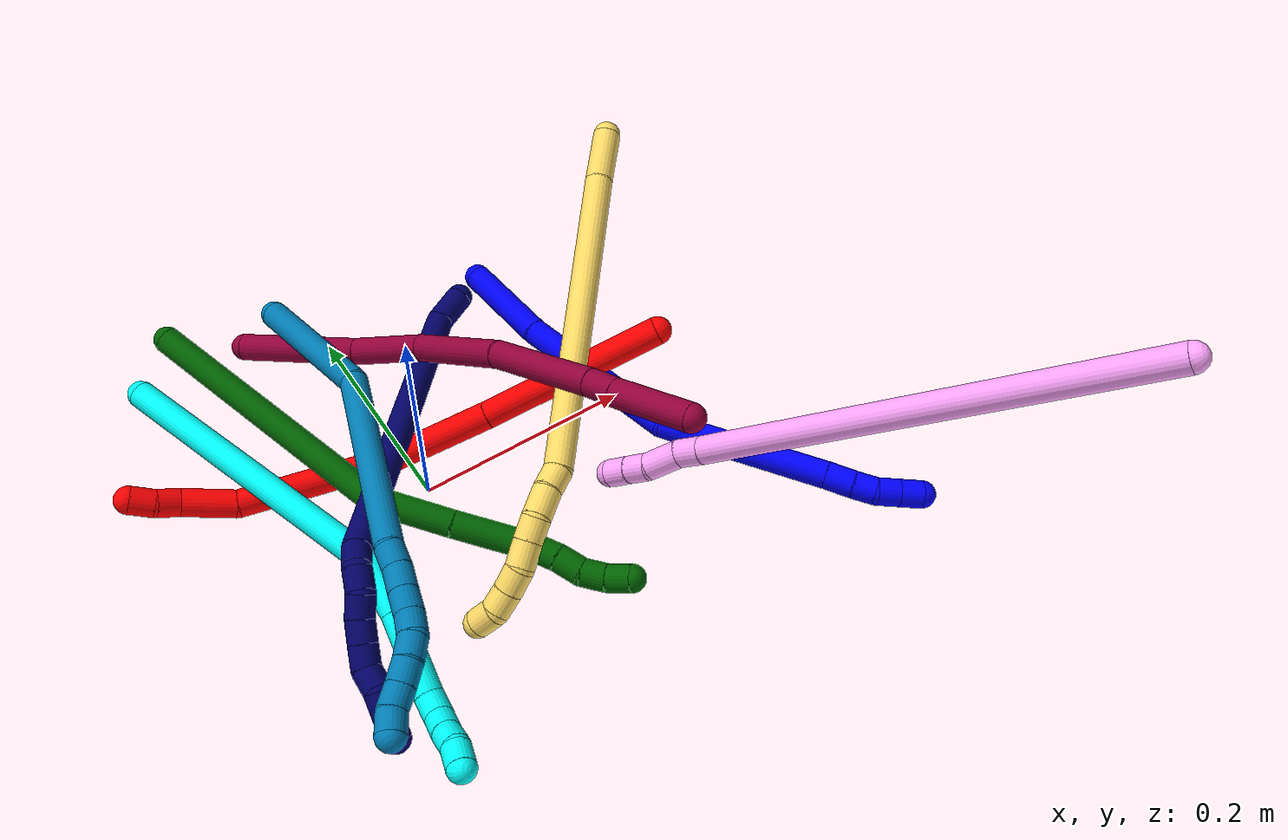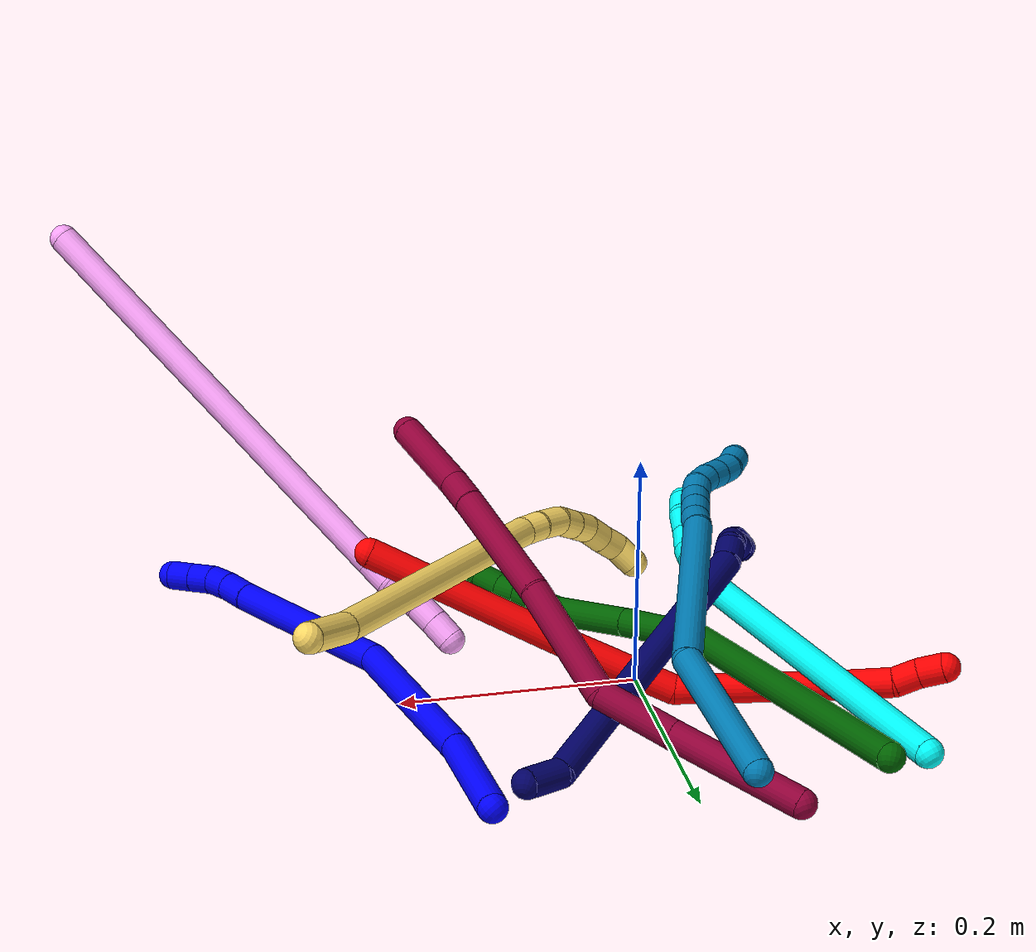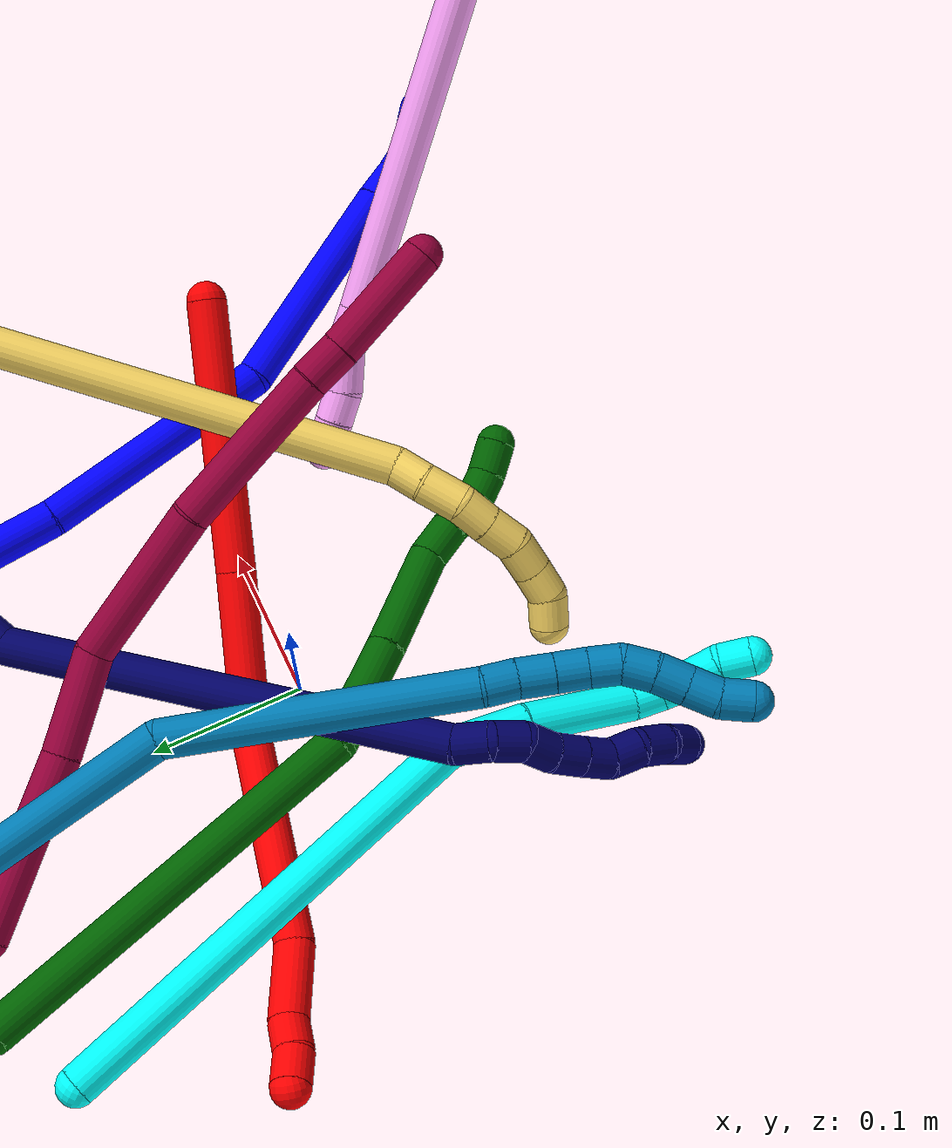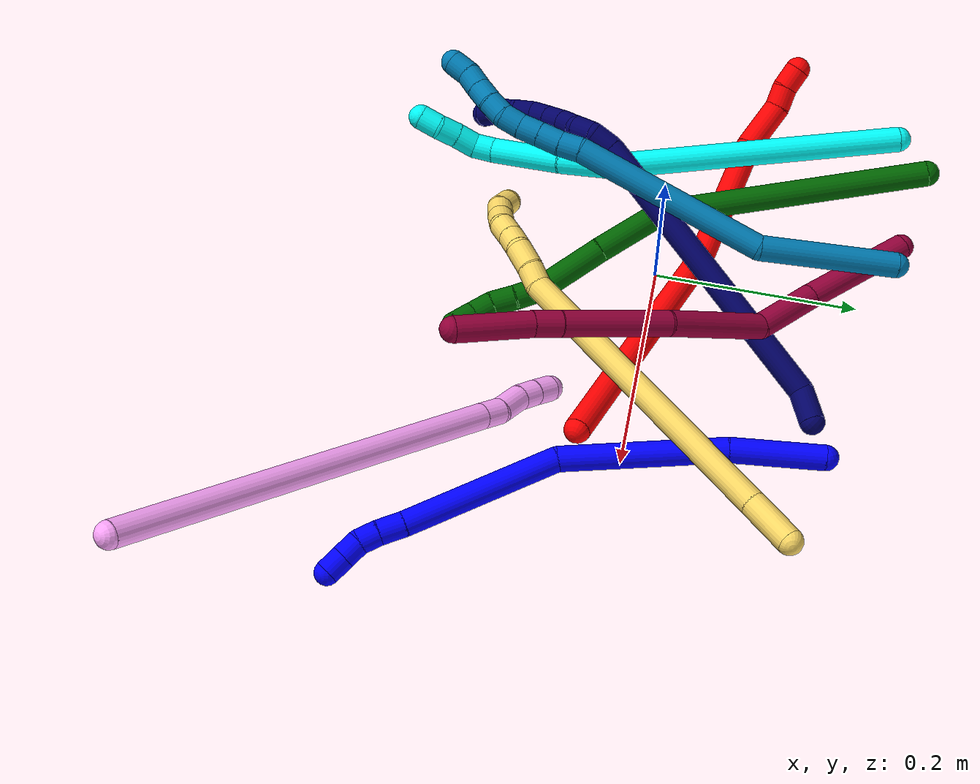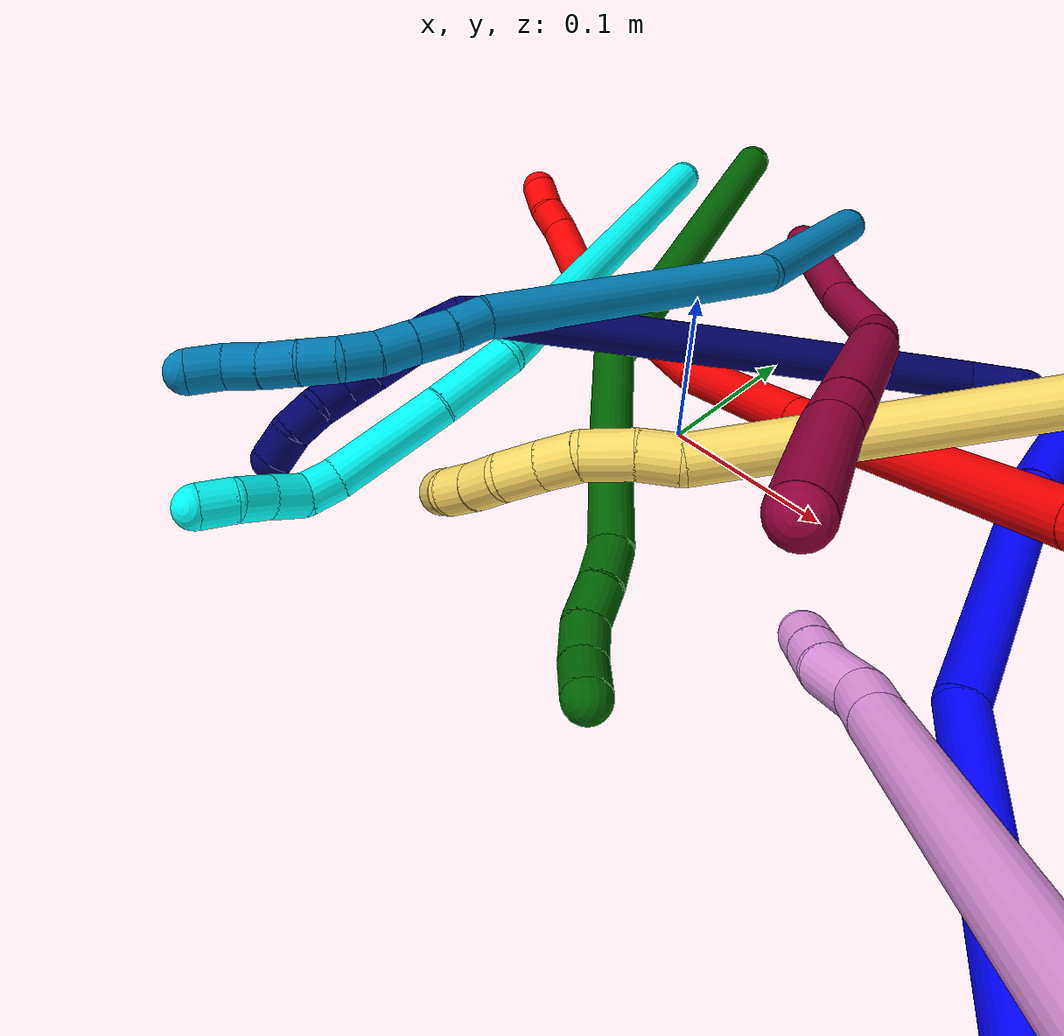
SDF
<sdf version="1.7">
 <world name="default">
  <plugin name="TubeGeneratorPlugin" filename="libtube_generator_plugin.so"/>
  <model name="photoneo_s_sensor">
   <static>1</static>
   <pose>0 0 2 1.57079 1.57079 3.14159</pose>
   <link name="link">
    <inertial><mass>0.1</mass></inertial>
    <sensor name="sensor" type="depth">
     <update_rate>30</update_rate>
     <camera>
      <horizontal_fov>1.22</horizontal_fov>
      <image><width>1920</width><height>1200</height><format>B8G8R8</format></image>
      <clip><near>0.1</near><far>4</far></clip>
      <depth_camera><output>points</output></depth_camera>
     </camera>
     <plugin name="camera_plugin" filename="libgazebo_ros_depth_camera.so">
      <baseline>0.2</baseline>
      <alwaysOn>1</alwaysOn>
      <updateRate>0.0</updateRate>
      <cameraName>camera_ir</cameraName>
      <imageTopicName>/camera/color/image_raw</imageTopicName>
      <cameraInfoTopicName>/camera/color/camera_info</cameraInfoTopicName>
      <depthImageTopicName>/camera/depth/image_raw</depthImageTopicName>
      <depthImageCameraInfoTopicName>/camera/depth/camera_info</depthImageCameraInfoTopicName>
      <pointCloudTopicName>/camera/depth/points</pointCloudTopicName>
      <frameName>fr_optical</frameName>
      <pointCloudCutoff>0.1</pointCloudCutoff>
      <pointCloudCutoffMax>2.0</pointCloudCutoffMax>
      <distortionK1>0</distortionK1>
      <distortionK2>0</distortionK2>
      <distortionK3>0</distortionK3>
      <distortionT1>0</distortionT1>
      <distortionT2>0</distortionT2>
      <CxPrime>0</CxPrime>
      <Cx>0</Cx>
      <Cy>0</Cy>
      <focalLength>0</focalLength>
      <hackBaseline>0</hackBaseline>
     </plugin>
    </sensor>
   </link>
  </model>
  <gravity>0 0 -9.8</gravity>
  <magnetic_field>6e-06 2.3e-05 -4.2e-05</magnetic_field>
  <atmosphere type="adiabatic"/>
  <physics name="default_physics" default="0" type="ode">
   <max_step_size>0.003</max_step_size>
   <real_time_factor>1</real_time_factor>
   <real_time_update_rate>1000</real_time_update_rate>
   <max_contacts>10000</max_contacts>
   <ode>
    <solver>
     <type>quick</type>
     <iters>100</iters>
     <sor>1.3</sor>
     <use_dynamic_moi_rescaling>0</use_dynamic_moi_rescaling>
    </solver>
    <constraints>
     <contact_max_correcting_vel>0</contact_max_correcting_vel>
     <contact_surface_layer>0.001</contact_surface_layer>
     <cfm>0</cfm>
     <erp>0.2</erp>
    </constraints>
   </ode>
  </physics>
  <scene><ambient>0.4 0.4 0.4 1</ambient><background>0.7 0.7 0.7 1</background><shadows>0</shadows></scene>
  <audio><device>default</device></audio>
  <spherical_coordinates>
   <surface_model>EARTH_WGS84</surface_model>
   <latitude_deg>0</latitude_deg>
   <longitude_deg>0</longitude_deg>
   <elevation>0</elevation>
   <heading_deg>0</heading_deg>
  </spherical_coordinates>
  <model name="bin">
   <static>1</static>
   <link name="bottom">
    <collision name="collision-bottom">
     <pose>0 0 -0.01 0 -0 0</pose>
     <geometry><box><size>0.8 0.6 0.02</size></box></geometry>
     <surface>
      <friction><ode><mu>100</mu><mu2>100</mu2></ode></friction>
      <contact><collide_bitmask>65535</collide_bitmask></contact>
     </surface>
    </collision>
   </link>
   <link name="west_wall">
    <collision name="collision-west_wall">
     <pose>-0.41 0 0.1 0 -0 0</pose>
     <geometry><box><size>0.02 0.6 0.2</size></box></geometry>
     <surface>
      <friction><ode><mu>100</mu><mu2>100</mu2></ode></friction>
      <contact><collide_bitmask>65535</collide_bitmask></contact>
     </surface>
    </collision>
   </link>
   <link name="east_wall">
    <collision name="collision-east_wall">
     <pose>0.41 0 0.1 0 -0 0</pose>
     <geometry><box><size>0.02 0.6 0.2</size></box></geometry>
     <surface>
      <friction><ode><mu>100</mu><mu2>100</mu2></ode></friction>
      <contact><collide_bitmask>65535</collide_bitmask></contact>
     </surface>
    </collision>
   </link>
   <link name="south_wall">
    <collision name="collision-south_wall">
     <pose>0 -0.31 0.1 0 -0 0</pose>
     <geometry><box><size>0.8 0.02 0.2</size></box></geometry>
     <surface>
      <friction><ode><mu>100</mu><mu2>100</mu2></ode></friction>
      <contact><collide_bitmask>65535</collide_bitmask></contact>
     </surface>
    </collision>
   </link>
   <link name="north_wall">
    <collision name="collision-north_wall">
     <pose>0 0.31 0.1 0 -0 0</pose>
     <geometry><box><size>0.8 0.02 0.2</size></box></geometry>
     <surface>
      <friction><ode><mu>100</mu><mu2>100</mu2></ode></friction>
      <contact><collide_bitmask>65535</collide_bitmask></contact>
     </surface>
    </collision>
   </link>
  </model>
  <model name="1">
   <static>0</static>
   <link name="1">
    <collision name="collision-cylinder-e_1_1_4">
     <pose>0.013761 -0.033315 0.029308 0.849297 0.300728 0.136798</pose>
     <geometry><cylinder><radius>0.0125</radius><length>0.092913</length></cylinder></geometry>
     <surface>
      <friction><ode><mu>1.16</mu><mu2>1.16</mu2><slip1>0</slip1><slip2>0</slip2></ode></friction>
      <contact><ode><kp>1e+06</kp><kd>1</kd><max_vel>0</max_vel><min_depth>0.001</min_depth></ode></contact>
     </surface>
    </collision>
    <visual name="visual-cylinder-e_1_1_4">
     <pose>0.013761 -0.033315 0.029308 0.849297 0.300728 0.136798</pose>
     <geometry><cylinder><radius>0.0125</radius><length>0.092913</length></cylinder></geometry>
     <material><ambient>0 0 1 1</ambient></material>
    </visual>
    <collision name="collision-cylinder-e_2_4_5">
     <pose>0.058813 -0.117606 0.114356 0.740785 0.392737 0.154191</pose>
     <geometry><cylinder><radius>0.0125</radius><length>0.163519</length></cylinder></geometry>
     <surface>
      <friction><ode><mu>1.16</mu><mu2>1.16</mu2><slip1>0</slip1><slip2>0</slip2></ode></friction>
      <contact><ode><kp>1e+06</kp><kd>1</kd><max_vel>0</max_vel><min_depth>0.001</min_depth></ode></contact>
     </surface>
    </collision>
    <visual name="visual-cylinder-e_2_4_5">
     <pose>0.058813 -0.117606 0.114356 0.740785 0.392737 0.154191</pose>
     <geometry><cylinder><radius>0.0125</radius><length>0.163519</length></cylinder></geometry>
     <material><ambient>0 0 1 1</ambient></material>
    </visual>
    <collision name="collision-cylinder-e_3_5_6">
     <pose>0.131842 -0.192563 0.23232 0.367858 0.559235 0.106733</pose>
     <geometry><cylinder><radius>0.0125</radius><length>0.157341</length></cylinder></geometry>
     <surface>
      <friction><ode><mu>1.16</mu><mu2>1.16</mu2><slip1>0</slip1><slip2>0</slip2></ode></friction>
      <contact><ode><kp>1e+06</kp><kd>1</kd><max_vel>0</max_vel><min_depth>0.001</min_depth></ode></contact>
     </surface>
    </collision>
    <visual name="visual-cylinder-e_3_5_6">
     <pose>0.131842 -0.192563 0.23232 0.367858 0.559235 0.106733</pose>
     <geometry><cylinder><radius>0.0125</radius><length>0.157341</length></cylinder></geometry>
     <material><ambient>0 0 1 1</ambient></material>
    </visual>
    <collision name="collision-cylinder-e_4_6_7">
     <pose>0.179793 -0.221125 0.304692 0.424069 0.509073 0.111901</pose>
     <geometry><cylinder><radius>0.0125</radius><length>0.025499</length></cylinder></geometry>
     <surface>
      <friction><ode><mu>1.16</mu><mu2>1.16</mu2><slip1>0</slip1><slip2>0</slip2></ode></friction>
      <contact><ode><kp>1e+06</kp><kd>1</kd><max_vel>0</max_vel><min_depth>0.001</min_depth></ode></contact>
     </surface>
    </collision>
    <visual name="visual-cylinder-e_4_6_7">
     <pose>0.179793 -0.221125 0.304692 0.424069 0.509073 0.111901</pose>
     <geometry><cylinder><radius>0.0125</radius><length>0.025499</length></cylinder></geometry>
     <material><ambient>0 0 1 1</ambient></material>
    </visual>
    <collision name="collision-cylinder-e_5_7_8">
     <pose>0.191664 -0.228524 0.322684 0.344812 0.596242 0.106914</pose>
     <geometry><cylinder><radius>0.0125</radius><length>0.020148</length></cylinder></geometry>
     <surface>
      <friction><ode><mu>1.16</mu><mu2>1.16</mu2><slip1>0</slip1><slip2>0</slip2></ode></friction>
      <contact><ode><kp>1e+06</kp><kd>1</kd><max_vel>0</max_vel><min_depth>0.001</min_depth></ode></contact>
     </surface>
    </collision>
    <visual name="visual-cylinder-e_5_7_8">
     <pose>0.191664 -0.228524 0.322684 0.344812 0.596242 0.106914</pose>
     <geometry><cylinder><radius>0.0125</radius><length>0.020148</length></cylinder></geometry>
     <material><ambient>0 0 1 1</ambient></material>
    </visual>
    <collision name="collision-cylinder-e_6_8_9">
     <pose>0.204213 -0.231158 0.337788 -0.025344 0.759342 -0.010113</pose>
     <geometry><cylinder><radius>0.0125</radius><length>0.020023</length></cylinder></geometry>
     <surface>
      <friction><ode><mu>1.16</mu><mu2>1.16</mu2><slip1>0</slip1><slip2>0</slip2></ode></friction>
      <contact><ode><kp>1e+06</kp><kd>1</kd><max_vel>0</max_vel><min_depth>0.001</min_depth></ode></contact>
     </surface>
    </collision>
    <visual name="visual-cylinder-e_6_8_9">
     <pose>0.204213 -0.231158 0.337788 -0.025344 0.759342 -0.010113</pose>
     <geometry><cylinder><radius>0.0125</radius><length>0.020023</length></cylinder></geometry>
     <material><ambient>0 0 1 1</ambient></material>
    </visual>
    <collision name="collision-cylinder-e_7_9_2">
     <pose>0.218136 -0.230765 0.352542 -0.027844 0.753199 -0.011012</pose>
     <geometry><cylinder><radius>0.0125</radius><length>0.020556</length></cylinder></geometry>
     <surface>
      <friction><ode><mu>1.16</mu><mu2>1.16</mu2><slip1>0</slip1><slip2>0</slip2></ode></friction>
      <contact><ode><kp>1e+06</kp><kd>1</kd><max_vel>0</max_vel><min_depth>0.001</min_depth></ode></contact>
     </surface>
    </collision>
    <visual name="visual-cylinder-e_7_9_2">
     <pose>0.218136 -0.230765 0.352542 -0.027844 0.753199 -0.011012</pose>
     <geometry><cylinder><radius>0.0125</radius><length>0.020556</length></cylinder></geometry>
     <material><ambient>0 0 1 1</ambient></material>
    </visual>
    <collision name="collision-sphere-2">
     <pose>0.225166 -0.230556 0.360037 0 -0 0</pose>
     <geometry><sphere><radius>0.0125</radius></sphere></geometry>
     <surface>
      <friction><ode><mu>1.16</mu><mu2>1.16</mu2><slip1>0</slip1><slip2>0</slip2></ode></friction>
      <contact><ode><kp>1e+06</kp><kd>1</kd><max_vel>0</max_vel><min_depth>0.001</min_depth></ode></contact>
     </surface>
    </collision>
    <visual name="visual-sphere-2">
     <pose>0.225166 -0.230556 0.360037 0 -0 0</pose>
     <geometry><sphere><radius>0.0125</radius></sphere></geometry>
     <material><ambient>0 0 1 1</ambient></material>
    </visual>
    <collision name="collision-sphere-9">
     <pose>0.211106 -0.230974 0.345047 0 -0 0</pose>
     <geometry><sphere><radius>0.0125</radius></sphere></geometry>
     <surface>
      <friction><ode><mu>1.16</mu><mu2>1.16</mu2><slip1>0</slip1><slip2>0</slip2></ode></friction>
      <contact><ode><kp>1e+06</kp><kd>1</kd><max_vel>0</max_vel><min_depth>0.001</min_depth></ode></contact>
     </surface>
    </collision>
    <visual name="visual-sphere-9">
     <pose>0.211106 -0.230974 0.345047 0 -0 0</pose>
     <geometry><sphere><radius>0.0125</radius></sphere></geometry>
     <material><ambient>0 0 1 1</ambient></material>
    </visual>
    <collision name="collision-sphere-4">
     <pose>0.027522 -0.06663 0.058616 0 -0 0</pose>
     <geometry><sphere><radius>0.0125</radius></sphere></geometry>
     <surface>
      <friction><ode><mu>1.16</mu><mu2>1.16</mu2><slip1>0</slip1><slip2>0</slip2></ode></friction>
      <contact><ode><kp>1e+06</kp><kd>1</kd><max_vel>0</max_vel><min_depth>0.001</min_depth></ode></contact>
     </surface>
    </collision>
    <visual name="visual-sphere-4">
     <pose>0.027522 -0.06663 0.058616 0 -0 0</pose>
     <geometry><sphere><radius>0.0125</radius></sphere></geometry>
     <material><ambient>0 0 1 1</ambient></material>
    </visual>
    <collision name="collision-sphere-1">
     <geometry><sphere><radius>0.0125</radius></sphere></geometry>
     <surface>
      <friction><ode><mu>1.16</mu><mu2>1.16</mu2><slip1>0</slip1><slip2>0</slip2></ode></friction>
      <contact><ode><kp>1e+06</kp><kd>1</kd><max_vel>0</max_vel><min_depth>0.001</min_depth></ode></contact>
     </surface>
    </collision>
    <visual name="visual-sphere-1">
     <geometry><sphere><radius>0.0125</radius></sphere></geometry>
     <material><ambient>0 0 1 1</ambient></material>
    </visual>
    <collision name="collision-sphere-8">
     <pose>0.197321 -0.231342 0.330529 0 -0 0</pose>
     <geometry><sphere><radius>0.0125</radius></sphere></geometry>
     <surface>
      <friction><ode><mu>1.16</mu><mu2>1.16</mu2><slip1>0</slip1><slip2>0</slip2></ode></friction>
      <contact><ode><kp>1e+06</kp><kd>1</kd><max_vel>0</max_vel><min_depth>0.001</min_depth></ode></contact>
     </surface>
    </collision>
    <visual name="visual-sphere-8">
     <pose>0.197321 -0.231342 0.330529 0 -0 0</pose>
     <geometry><sphere><radius>0.0125</radius></sphere></geometry>
     <material><ambient>0 0 1 1</ambient></material>
    </visual>
    <collision name="collision-sphere-5">
     <pose>0.090104 -0.168582 0.170096 0 -0 0</pose>
     <geometry><sphere><radius>0.0125</radius></sphere></geometry>
     <surface>
      <friction><ode><mu>1.16</mu><mu2>1.16</mu2><slip1>0</slip1><slip2>0</slip2></ode></friction>
      <contact><ode><kp>1e+06</kp><kd>1</kd><max_vel>0</max_vel><min_depth>0.001</min_depth></ode></contact>
     </surface>
    </collision>
    <visual name="visual-sphere-5">
     <pose>0.090104 -0.168582 0.170096 0 -0 0</pose>
     <geometry><sphere><radius>0.0125</radius></sphere></geometry>
     <material><ambient>0 0 1 1</ambient></material>
    </visual>
    <collision name="collision-sphere-6">
     <pose>0.173579 -0.216544 0.294545 0 -0 0</pose>
     <geometry><sphere><radius>0.0125</radius></sphere></geometry>
     <surface>
      <friction><ode><mu>1.16</mu><mu2>1.16</mu2><slip1>0</slip1><slip2>0</slip2></ode></friction>
      <contact><ode><kp>1e+06</kp><kd>1</kd><max_vel>0</max_vel><min_depth>0.001</min_depth></ode></contact>
     </surface>
    </collision>
    <visual name="visual-sphere-6">
     <pose>0.173579 -0.216544 0.294545 0 -0 0</pose>
     <geometry><sphere><radius>0.0125</radius></sphere></geometry>
     <material><ambient>0 0 1 1</ambient></material>
    </visual>
    <collision name="collision-sphere-7">
     <pose>0.186007 -0.225706 0.314839 0 -0 0</pose>
     <geometry><sphere><radius>0.0125</radius></sphere></geometry>
     <surface>
      <friction><ode><mu>1.16</mu><mu2>1.16</mu2><slip1>0</slip1><slip2>0</slip2></ode></friction>
      <contact><ode><kp>1e+06</kp><kd>1</kd><max_vel>0</max_vel><min_depth>0.001</min_depth></ode></contact>
     </surface>
    </collision>
    <visual name="visual-sphere-7">
     <pose>0.186007 -0.225706 0.314839 0 -0 0</pose>
     <geometry><sphere><radius>0.0125</radius></sphere></geometry>
     <material><ambient>0 0 1 1</ambient></material>
    </visual>
    <inertial>
     <pose>0.097318 -0.144479 0.172515 0 -0 0</pose>
     <mass>0.5</mass>
     <inertia><ixx>0.000799</ixx><ixy>0</ixy><ixz>0</ixz><iyy>0.000727</iyy><iyz>0</iyz><izz>7e-05</izz></inertia>
    </inertial>
   </link>
   <pose>0.162126 0.191928 0.011498 0.31651 0.874543 -0.392799</pose>
  </model>
  <model name="2">
   <static>0</static>
   <link name="2">
    <collision name="collision-cylinder-e_1_1_4">
     <pose>0.004699 0.004672 -0.084354 -3.08626 0.055566 -1.57508</pose>
     <geometry><cylinder><radius>0.0125</radius><length>0.169228</length></cylinder></geometry>
     <surface>
      <friction><ode><mu>1.16</mu><mu2>1.16</mu2><slip1>0</slip1><slip2>0</slip2></ode></friction>
      <contact><ode><kp>1e+06</kp><kd>1</kd><max_vel>0</max_vel><min_depth>0.001</min_depth></ode></contact>
     </surface>
    </collision>
    <visual name="visual-cylinder-e_1_1_4">
     <pose>0.004699 0.004672 -0.084354 -3.08626 0.055566 -1.57508</pose>
     <geometry><cylinder><radius>0.0125</radius><length>0.169228</length></cylinder></geometry>
     <material><ambient>1 0 0 1</ambient></material>
    </visual>
    <collision name="collision-cylinder-e_2_4_5">
     <pose>0.011067 0.013626 -0.220899 -3.05972 0.031842 -0.74153</pose>
     <geometry><cylinder><radius>0.0125</radius><length>0.104784</length></cylinder></geometry>
     <surface>
      <friction><ode><mu>1.16</mu><mu2>1.16</mu2><slip1>0</slip1><slip2>0</slip2></ode></friction>
      <contact><ode><kp>1e+06</kp><kd>1</kd><max_vel>0</max_vel><min_depth>0.001</min_depth></ode></contact>
     </surface>
    </collision>
    <visual name="visual-cylinder-e_2_4_5">
     <pose>0.011067 0.013626 -0.220899 -3.05972 0.031842 -0.74153</pose>
     <geometry><cylinder><radius>0.0125</radius><length>0.104784</length></cylinder></geometry>
     <material><ambient>1 0 0 1</ambient></material>
    </visual>
    <collision name="collision-cylinder-e_3_5_6">
     <pose>-0.012821 0.029422 -0.333546 -2.95342 -0.393579 2.25743</pose>
     <geometry><cylinder><radius>0.0125</radius><length>0.133278</length></cylinder></geometry>
     <surface>
      <friction><ode><mu>1.16</mu><mu2>1.16</mu2><slip1>0</slip1><slip2>0</slip2></ode></friction>
      <contact><ode><kp>1e+06</kp><kd>1</kd><max_vel>0</max_vel><min_depth>0.001</min_depth></ode></contact>
     </surface>
    </collision>
    <visual name="visual-cylinder-e_3_5_6">
     <pose>-0.012821 0.029422 -0.333546 -2.95342 -0.393579 2.25743</pose>
     <geometry><cylinder><radius>0.0125</radius><length>0.133278</length></cylinder></geometry>
     <material><ambient>1 0 0 1</ambient></material>
    </visual>
    <collision name="collision-cylinder-e_4_6_7">
     <pose>-0.047796 0.052322 -0.413509 -2.61317 -0.395104 1.27397</pose>
     <geometry><cylinder><radius>0.0125</radius><length>0.048943</length></cylinder></geometry>
     <surface>
      <friction><ode><mu>1.16</mu><mu2>1.16</mu2><slip1>0</slip1><slip2>0</slip2></ode></friction>
      <contact><ode><kp>1e+06</kp><kd>1</kd><max_vel>0</max_vel><min_depth>0.001</min_depth></ode></contact>
     </surface>
    </collision>
    <visual name="visual-cylinder-e_4_6_7">
     <pose>-0.047796 0.052322 -0.413509 -2.61317 -0.395104 1.27397</pose>
     <geometry><cylinder><radius>0.0125</radius><length>0.048943</length></cylinder></geometry>
     <material><ambient>1 0 0 1</ambient></material>
    </visual>
    <collision name="collision-cylinder-e_5_7_8">
     <pose>-0.064223 0.067257 -0.440355 -2.69136 -0.710027 2.0349</pose>
     <geometry><cylinder><radius>0.0125</radius><length>0.021502</length></cylinder></geometry>
     <surface>
      <friction><ode><mu>1.16</mu><mu2>1.16</mu2><slip1>0</slip1><slip2>0</slip2></ode></friction>
      <contact><ode><kp>1e+06</kp><kd>1</kd><max_vel>0</max_vel><min_depth>0.001</min_depth></ode></contact>
     </surface>
    </collision>
    <visual name="visual-cylinder-e_5_7_8">
     <pose>-0.064223 0.067257 -0.440355 -2.69136 -0.710027 2.0349</pose>
     <geometry><cylinder><radius>0.0125</radius><length>0.021502</length></cylinder></geometry>
     <material><ambient>1 0 0 1</ambient></material>
    </visual>
    <collision name="collision-cylinder-e_6_8_2">
     <pose>-0.076852 0.076634 -0.455335 -2.4899 -0.529268 1.35192</pose>
     <geometry><cylinder><radius>0.0125</radius><length>0.022265</length></cylinder></geometry>
     <surface>
      <friction><ode><mu>1.16</mu><mu2>1.16</mu2><slip1>0</slip1><slip2>0</slip2></ode></friction>
      <contact><ode><kp>1e+06</kp><kd>1</kd><max_vel>0</max_vel><min_depth>0.001</min_depth></ode></contact>
     </surface>
    </collision>
    <visual name="visual-cylinder-e_6_8_2">
     <pose>-0.076852 0.076634 -0.455335 -2.4899 -0.529268 1.35192</pose>
     <geometry><cylinder><radius>0.0125</radius><length>0.022265</length></cylinder></geometry>
     <material><ambient>1 0 0 1</ambient></material>
    </visual>
    <collision name="collision-sphere-2">
     <pose>-0.082473 0.082462 -0.462975 0 -0 0</pose>
     <geometry><sphere><radius>0.0125</radius></sphere></geometry>
     <surface>
      <friction><ode><mu>1.16</mu><mu2>1.16</mu2><slip1>0</slip1><slip2>0</slip2></ode></friction>
      <contact><ode><kp>1e+06</kp><kd>1</kd><max_vel>0</max_vel><min_depth>0.001</min_depth></ode></contact>
     </surface>
    </collision>
    <visual name="visual-sphere-2">
     <pose>-0.082473 0.082462 -0.462975 0 -0 0</pose>
     <geometry><sphere><radius>0.0125</radius></sphere></geometry>
     <material><ambient>1 0 0 1</ambient></material>
    </visual>
    <collision name="collision-sphere-4">
     <pose>0.009399 0.009344 -0.168708 0 -0 0</pose>
     <geometry><sphere><radius>0.0125</radius></sphere></geometry>
     <surface>
      <friction><ode><mu>1.16</mu><mu2>1.16</mu2><slip1>0</slip1><slip2>0</slip2></ode></friction>
      <contact><ode><kp>1e+06</kp><kd>1</kd><max_vel>0</max_vel><min_depth>0.001</min_depth></ode></contact>
     </surface>
    </collision>
    <visual name="visual-sphere-4">
     <pose>0.009399 0.009344 -0.168708 0 -0 0</pose>
     <geometry><sphere><radius>0.0125</radius></sphere></geometry>
     <material><ambient>1 0 0 1</ambient></material>
    </visual>
    <collision name="collision-sphere-1">
     <geometry><sphere><radius>0.0125</radius></sphere></geometry>
     <surface>
      <friction><ode><mu>1.16</mu><mu2>1.16</mu2><slip1>0</slip1><slip2>0</slip2></ode></friction>
      <contact><ode><kp>1e+06</kp><kd>1</kd><max_vel>0</max_vel><min_depth>0.001</min_depth></ode></contact>
     </surface>
    </collision>
    <visual name="visual-sphere-1">
     <geometry><sphere><radius>0.0125</radius></sphere></geometry>
     <material><ambient>1 0 0 1</ambient></material>
    </visual>
    <collision name="collision-sphere-8">
     <pose>-0.071232 0.070805 -0.447696 0 -0 0</pose>
     <geometry><sphere><radius>0.0125</radius></sphere></geometry>
     <surface>
      <friction><ode><mu>1.16</mu><mu2>1.16</mu2><slip1>0</slip1><slip2>0</slip2></ode></friction>
      <contact><ode><kp>1e+06</kp><kd>1</kd><max_vel>0</max_vel><min_depth>0.001</min_depth></ode></contact>
     </surface>
    </collision>
    <visual name="visual-sphere-8">
     <pose>-0.071232 0.070805 -0.447696 0 -0 0</pose>
     <geometry><sphere><radius>0.0125</radius></sphere></geometry>
     <material><ambient>1 0 0 1</ambient></material>
    </visual>
    <collision name="collision-sphere-5">
     <pose>0.012735 0.017909 -0.273089 0 -0 0</pose>
     <geometry><sphere><radius>0.0125</radius></sphere></geometry>
     <surface>
      <friction><ode><mu>1.16</mu><mu2>1.16</mu2><slip1>0</slip1><slip2>0</slip2></ode></friction>
      <contact><ode><kp>1e+06</kp><kd>1</kd><max_vel>0</max_vel><min_depth>0.001</min_depth></ode></contact>
     </surface>
    </collision>
    <visual name="visual-sphere-5">
     <pose>0.012735 0.017909 -0.273089 0 -0 0</pose>
     <geometry><sphere><radius>0.0125</radius></sphere></geometry>
     <material><ambient>1 0 0 1</ambient></material>
    </visual>
    <collision name="collision-sphere-6">
     <pose>-0.038377 0.040935 -0.394004 0 -0 0</pose>
     <geometry><sphere><radius>0.0125</radius></sphere></geometry>
     <surface>
      <friction><ode><mu>1.16</mu><mu2>1.16</mu2><slip1>0</slip1><slip2>0</slip2></ode></friction>
      <contact><ode><kp>1e+06</kp><kd>1</kd><max_vel>0</max_vel><min_depth>0.001</min_depth></ode></contact>
     </surface>
    </collision>
    <visual name="visual-sphere-6">
     <pose>-0.038377 0.040935 -0.394004 0 -0 0</pose>
     <geometry><sphere><radius>0.0125</radius></sphere></geometry>
     <material><ambient>1 0 0 1</ambient></material>
    </visual>
    <collision name="collision-sphere-7">
     <pose>-0.057215 0.063709 -0.433014 0 -0 0</pose>
     <geometry><sphere><radius>0.0125</radius></sphere></geometry>
     <surface>
      <friction><ode><mu>1.16</mu><mu2>1.16</mu2><slip1>0</slip1><slip2>0</slip2></ode></friction>
      <contact><ode><kp>1e+06</kp><kd>1</kd><max_vel>0</max_vel><min_depth>0.001</min_depth></ode></contact>
     </surface>
    </collision>
    <visual name="visual-sphere-7">
     <pose>-0.057215 0.063709 -0.433014 0 -0 0</pose>
     <geometry><sphere><radius>0.0125</radius></sphere></geometry>
     <material><ambient>1 0 0 1</ambient></material>
    </visual>
    <inertial>
     <pose>-0.01037 0.023706 -0.243442 0 -0 0</pose>
     <mass>0.5</mass>
     <inertia>
      <ixx>-0.00037</ixx>
      <ixy>0</ixy>
      <ixz>0</ixz>
      <iyy>-0.000246</iyy>
      <iyz>0</iyz>
      <izz>-5.1e-05</izz>
     </inertia>
    </inertial>
   </link>
   <pose>0.216281 -0.03949 0.121212 0.845546 0.935989 0.710162</pose>
  </model>
  <model name="3">
   <static>0</static>
   <link name="3">
    <collision name="collision-cylinder-e_1_1_4">
     <pose>-0.007961 -0.093376 -0.111943 2.44638 -0.05456 -0.150339</pose>
     <geometry><cylinder><radius>0.0125</radius><length>0.291985</length></cylinder></geometry>
     <surface>
      <friction><ode><mu>1.16</mu><mu2>1.16</mu2><slip1>0</slip1><slip2>0</slip2></ode></friction>
      <contact><ode><kp>1e+06</kp><kd>1</kd><max_vel>0</max_vel><min_depth>0.001</min_depth></ode></contact>
     </surface>
    </collision>
    <visual name="visual-cylinder-e_1_1_4">
     <pose>-0.007961 -0.093376 -0.111943 2.44638 -0.05456 -0.150339</pose>
     <geometry><cylinder><radius>0.0125</radius><length>0.291985</length></cylinder></geometry>
     <material><ambient>0.003922 1 0.996078 1</ambient></material>
    </visual>
    <collision name="collision-cylinder-e_2_4_5">
     <pose>-0.010751 -0.208688 -0.236737 2.10075 0.2007 0.34782</pose>
     <geometry><cylinder><radius>0.0125</radius><length>0.051886</length></cylinder></geometry>
     <surface>
      <friction><ode><mu>1.16</mu><mu2>1.16</mu2><slip1>0</slip1><slip2>0</slip2></ode></friction>
      <contact><ode><kp>1e+06</kp><kd>1</kd><max_vel>0</max_vel><min_depth>0.001</min_depth></ode></contact>
     </surface>
    </collision>
    <visual name="visual-cylinder-e_2_4_5">
     <pose>-0.010751 -0.208688 -0.236737 2.10075 0.2007 0.34782</pose>
     <geometry><cylinder><radius>0.0125</radius><length>0.051886</length></cylinder></geometry>
     <material><ambient>0.003922 1 0.996078 1</ambient></material>
    </visual>
    <collision name="collision-cylinder-e_3_5_6">
     <pose>0.00411 -0.262659 -0.264437 2.00483 0.267816 0.415753</pose>
     <geometry><cylinder><radius>0.0125</radius><length>0.073232</length></cylinder></geometry>
     <surface>
      <friction><ode><mu>1.16</mu><mu2>1.16</mu2><slip1>0</slip1><slip2>0</slip2></ode></friction>
      <contact><ode><kp>1e+06</kp><kd>1</kd><max_vel>0</max_vel><min_depth>0.001</min_depth></ode></contact>
     </surface>
    </collision>
    <visual name="visual-cylinder-e_3_5_6">
     <pose>0.00411 -0.262659 -0.264437 2.00483 0.267816 0.415753</pose>
     <geometry><cylinder><radius>0.0125</radius><length>0.073232</length></cylinder></geometry>
     <material><ambient>0.003922 1 0.996078 1</ambient></material>
    </visual>
    <collision name="collision-cylinder-e_4_6_7">
     <pose>0.016978 -0.302329 -0.285565 2.25917 0.3111 0.641202</pose>
     <geometry><cylinder><radius>0.0125</radius><length>0.020766</length></cylinder></geometry>
     <surface>
      <friction><ode><mu>1.16</mu><mu2>1.16</mu2><slip1>0</slip1><slip2>0</slip2></ode></friction>
      <contact><ode><kp>1e+06</kp><kd>1</kd><max_vel>0</max_vel><min_depth>0.001</min_depth></ode></contact>
     </surface>
    </collision>
    <visual name="visual-cylinder-e_4_6_7">
     <pose>0.016978 -0.302329 -0.285565 2.25917 0.3111 0.641202</pose>
     <geometry><cylinder><radius>0.0125</radius><length>0.020766</length></cylinder></geometry>
     <material><ambient>0.003922 1 0.996078 1</ambient></material>
    </visual>
    <collision name="collision-cylinder-e_5_7_8">
     <pose>0.025255 -0.313507 -0.300778 2.76396 0.487794 1.83187</pose>
     <geometry><cylinder><radius>0.0125</radius><length>0.021758</length></cylinder></geometry>
     <surface>
      <friction><ode><mu>1.16</mu><mu2>1.16</mu2><slip1>0</slip1><slip2>0</slip2></ode></friction>
      <contact><ode><kp>1e+06</kp><kd>1</kd><max_vel>0</max_vel><min_depth>0.001</min_depth></ode></contact>
     </surface>
    </collision>
    <visual name="visual-cylinder-e_5_7_8">
     <pose>0.025255 -0.313507 -0.300778 2.76396 0.487794 1.83187</pose>
     <geometry><cylinder><radius>0.0125</radius><length>0.021758</length></cylinder></geometry>
     <material><ambient>0.003922 1 0.996078 1</ambient></material>
    </visual>
    <collision name="collision-cylinder-e_6_8_9">
     <pose>0.034263 -0.320208 -0.318451 2.79485 0.398136 1.71178</pose>
     <geometry><cylinder><radius>0.0125</radius><length>0.020164</length></cylinder></geometry>
     <surface>
      <friction><ode><mu>1.16</mu><mu2>1.16</mu2><slip1>0</slip1><slip2>0</slip2></ode></friction>
      <contact><ode><kp>1e+06</kp><kd>1</kd><max_vel>0</max_vel><min_depth>0.001</min_depth></ode></contact>
     </surface>
    </collision>
    <visual name="visual-cylinder-e_6_8_9">
     <pose>0.034263 -0.320208 -0.318451 2.79485 0.398136 1.71178</pose>
     <geometry><cylinder><radius>0.0125</radius><length>0.020164</length></cylinder></geometry>
     <material><ambient>0.003922 1 0.996078 1</ambient></material>
    </visual>
    <collision name="collision-cylinder-e_7_9_2">
     <pose>0.043465 -0.328666 -0.333975 2.47839 0.551381 1.37556</pose>
     <geometry><cylinder><radius>0.0125</radius><length>0.02021</length></cylinder></geometry>
     <surface>
      <friction><ode><mu>1.16</mu><mu2>1.16</mu2><slip1>0</slip1><slip2>0</slip2></ode></friction>
      <contact><ode><kp>1e+06</kp><kd>1</kd><max_vel>0</max_vel><min_depth>0.001</min_depth></ode></contact>
     </surface>
    </collision>
    <visual name="visual-cylinder-e_7_9_2">
     <pose>0.043465 -0.328666 -0.333975 2.47839 0.551381 1.37556</pose>
     <geometry><cylinder><radius>0.0125</radius><length>0.02021</length></cylinder></geometry>
     <material><ambient>0.003922 1 0.996078 1</ambient></material>
    </visual>
    <collision name="collision-sphere-2">
     <pose>0.048759 -0.333965 -0.340757 0 -0 0</pose>
     <geometry><sphere><radius>0.0125</radius></sphere></geometry>
     <surface>
      <friction><ode><mu>1.16</mu><mu2>1.16</mu2><slip1>0</slip1><slip2>0</slip2></ode></friction>
      <contact><ode><kp>1e+06</kp><kd>1</kd><max_vel>0</max_vel><min_depth>0.001</min_depth></ode></contact>
     </surface>
    </collision>
    <visual name="visual-sphere-2">
     <pose>0.048759 -0.333965 -0.340757 0 -0 0</pose>
     <geometry><sphere><radius>0.0125</radius></sphere></geometry>
     <material><ambient>0.003922 1 0.996078 1</ambient></material>
    </visual>
    <collision name="collision-sphere-9">
     <pose>0.038172 -0.323367 -0.327192 0 -0 0</pose>
     <geometry><sphere><radius>0.0125</radius></sphere></geometry>
     <surface>
      <friction><ode><mu>1.16</mu><mu2>1.16</mu2><slip1>0</slip1><slip2>0</slip2></ode></friction>
      <contact><ode><kp>1e+06</kp><kd>1</kd><max_vel>0</max_vel><min_depth>0.001</min_depth></ode></contact>
     </surface>
    </collision>
    <visual name="visual-sphere-9">
     <pose>0.038172 -0.323367 -0.327192 0 -0 0</pose>
     <geometry><sphere><radius>0.0125</radius></sphere></geometry>
     <material><ambient>0.003922 1 0.996078 1</ambient></material>
    </visual>
    <collision name="collision-sphere-4">
     <pose>-0.015923 -0.186753 -0.223886 0 -0 0</pose>
     <geometry><sphere><radius>0.0125</radius></sphere></geometry>
     <surface>
      <friction><ode><mu>1.16</mu><mu2>1.16</mu2><slip1>0</slip1><slip2>0</slip2></ode></friction>
      <contact><ode><kp>1e+06</kp><kd>1</kd><max_vel>0</max_vel><min_depth>0.001</min_depth></ode></contact>
     </surface>
    </collision>
    <visual name="visual-sphere-4">
     <pose>-0.015923 -0.186753 -0.223886 0 -0 0</pose>
     <geometry><sphere><radius>0.0125</radius></sphere></geometry>
     <material><ambient>0.003922 1 0.996078 1</ambient></material>
    </visual>
    <collision name="collision-sphere-1">
     <geometry><sphere><radius>0.0125</radius></sphere></geometry>
     <surface>
      <friction><ode><mu>1.16</mu><mu2>1.16</mu2><slip1>0</slip1><slip2>0</slip2></ode></friction>
      <contact><ode><kp>1e+06</kp><kd>1</kd><max_vel>0</max_vel><min_depth>0.001</min_depth></ode></contact>
     </surface>
    </collision>
    <visual name="visual-sphere-1">
     <geometry><sphere><radius>0.0125</radius></sphere></geometry>
     <material><ambient>0.003922 1 0.996078 1</ambient></material>
    </visual>
    <collision name="collision-sphere-8">
     <pose>0.030354 -0.31705 -0.309711 0 -0 0</pose>
     <geometry><sphere><radius>0.0125</radius></sphere></geometry>
     <surface>
      <friction><ode><mu>1.16</mu><mu2>1.16</mu2><slip1>0</slip1><slip2>0</slip2></ode></friction>
      <contact><ode><kp>1e+06</kp><kd>1</kd><max_vel>0</max_vel><min_depth>0.001</min_depth></ode></contact>
     </surface>
    </collision>
    <visual name="visual-sphere-8">
     <pose>0.030354 -0.31705 -0.309711 0 -0 0</pose>
     <geometry><sphere><radius>0.0125</radius></sphere></geometry>
     <material><ambient>0.003922 1 0.996078 1</ambient></material>
    </visual>
    <collision name="collision-sphere-5">
     <pose>-0.005579 -0.230623 -0.249587 0 -0 0</pose>
     <geometry><sphere><radius>0.0125</radius></sphere></geometry>
     <surface>
      <friction><ode><mu>1.16</mu><mu2>1.16</mu2><slip1>0</slip1><slip2>0</slip2></ode></friction>
      <contact><ode><kp>1e+06</kp><kd>1</kd><max_vel>0</max_vel><min_depth>0.001</min_depth></ode></contact>
     </surface>
    </collision>
    <visual name="visual-sphere-5">
     <pose>-0.005579 -0.230623 -0.249587 0 -0 0</pose>
     <geometry><sphere><radius>0.0125</radius></sphere></geometry>
     <material><ambient>0.003922 1 0.996078 1</ambient></material>
    </visual>
    <collision name="collision-sphere-6">
     <pose>0.0138 -0.294696 -0.279286 0 -0 0</pose>
     <geometry><sphere><radius>0.0125</radius></sphere></geometry>
     <surface>
      <friction><ode><mu>1.16</mu><mu2>1.16</mu2><slip1>0</slip1><slip2>0</slip2></ode></friction>
      <contact><ode><kp>1e+06</kp><kd>1</kd><max_vel>0</max_vel><min_depth>0.001</min_depth></ode></contact>
     </surface>
    </collision>
    <visual name="visual-sphere-6">
     <pose>0.0138 -0.294696 -0.279286 0 -0 0</pose>
     <geometry><sphere><radius>0.0125</radius></sphere></geometry>
     <material><ambient>0.003922 1 0.996078 1</ambient></material>
    </visual>
    <collision name="collision-sphere-7">
     <pose>0.020157 -0.309963 -0.291845 0 -0 0</pose>
     <geometry><sphere><radius>0.0125</radius></sphere></geometry>
     <surface>
      <friction><ode><mu>1.16</mu><mu2>1.16</mu2><slip1>0</slip1><slip2>0</slip2></ode></friction>
      <contact><ode><kp>1e+06</kp><kd>1</kd><max_vel>0</max_vel><min_depth>0.001</min_depth></ode></contact>
     </surface>
    </collision>
    <visual name="visual-sphere-7">
     <pose>0.020157 -0.309963 -0.291845 0 -0 0</pose>
     <geometry><sphere><radius>0.0125</radius></sphere></geometry>
     <material><ambient>0.003922 1 0.996078 1</ambient></material>
    </visual>
    <inertial>
     <pose>-0.00022 -0.167052 -0.179958 0 -0 0</pose>
     <mass>0.5</mass>
     <inertia>
      <ixx>0.001819</ixx>
      <ixy>0</ixy>
      <ixz>0</ixz>
      <iyy>-0.001903</iyy>
      <iyz>0</iyz>
      <izz>0.001452</izz>
     </inertia>
    </inertial>
   </link>
   <pose>-0.177607 0.214972 0.032556 2.32206 -0.282167 -2.89922</pose>
  </model>
  <model name="4">
   <static>0</static>
   <link name="4">
    <collision name="collision-cylinder-e_1_1_4">
     <pose>-0.039723 0.006475 -0.197909 -3.10889 -0.197981 2.81521</pose>
     <geometry><cylinder><radius>0.0125</radius><length>0.40392</length></cylinder></geometry>
     <surface>
      <friction><ode><mu>1.16</mu><mu2>1.16</mu2><slip1>0</slip1><slip2>0</slip2></ode></friction>
      <contact><ode><kp>1e+06</kp><kd>1</kd><max_vel>0</max_vel><min_depth>0.001</min_depth></ode></contact>
     </surface>
    </collision>
    <visual name="visual-cylinder-e_1_1_4">
     <pose>-0.039723 0.006475 -0.197909 -3.10889 -0.197981 2.81521</pose>
     <geometry><cylinder><radius>0.0125</radius><length>0.40392</length></cylinder></geometry>
     <material><ambient>1 0.65098 0.996078 1</ambient></material>
    </visual>
    <collision name="collision-cylinder-e_2_4_5">
     <pose>-0.081889 0.01372 -0.407118 -3.0735 -0.212401 2.52311</pose>
     <geometry><cylinder><radius>0.0125</radius><length>0.023174</length></cylinder></geometry>
     <surface>
      <friction><ode><mu>1.16</mu><mu2>1.16</mu2><slip1>0</slip1><slip2>0</slip2></ode></friction>
      <contact><ode><kp>1e+06</kp><kd>1</kd><max_vel>0</max_vel><min_depth>0.001</min_depth></ode></contact>
     </surface>
    </collision>
    <visual name="visual-cylinder-e_2_4_5">
     <pose>-0.081889 0.01372 -0.407118 -3.0735 -0.212401 2.52311</pose>
     <geometry><cylinder><radius>0.0125</radius><length>0.023174</length></cylinder></geometry>
     <material><ambient>1 0.65098 0.996078 1</ambient></material>
    </visual>
    <collision name="collision-cylinder-e_3_5_6">
     <pose>-0.087815 0.011204 -0.433558 2.92786 -0.221127 -1.60508</pose>
     <geometry><cylinder><radius>0.0125</radius><length>0.031758</length></cylinder></geometry>
     <surface>
      <friction><ode><mu>1.16</mu><mu2>1.16</mu2><slip1>0</slip1><slip2>0</slip2></ode></friction>
      <contact><ode><kp>1e+06</kp><kd>1</kd><max_vel>0</max_vel><min_depth>0.001</min_depth></ode></contact>
     </surface>
    </collision>
    <visual name="visual-cylinder-e_3_5_6">
     <pose>-0.087815 0.011204 -0.433558 2.92786 -0.221127 -1.60508</pose>
     <geometry><cylinder><radius>0.0125</radius><length>0.031758</length></cylinder></geometry>
     <material><ambient>1 0.65098 0.996078 1</ambient></material>
    </visual>
    <collision name="collision-cylinder-e_4_6_7">
     <pose>-0.093489 0.008326 -0.458568 -3.10027 -0.218305 2.76883</pose>
     <geometry><cylinder><radius>0.0125</radius><length>0.020236</length></cylinder></geometry>
     <surface>
      <friction><ode><mu>1.16</mu><mu2>1.16</mu2><slip1>0</slip1><slip2>0</slip2></ode></friction>
      <contact><ode><kp>1e+06</kp><kd>1</kd><max_vel>0</max_vel><min_depth>0.001</min_depth></ode></contact>
     </surface>
    </collision>
    <visual name="visual-cylinder-e_4_6_7">
     <pose>-0.093489 0.008326 -0.458568 -3.10027 -0.218305 2.76883</pose>
     <geometry><cylinder><radius>0.0125</radius><length>0.020236</length></cylinder></geometry>
     <material><ambient>1 0.65098 0.996078 1</ambient></material>
    </visual>
    <collision name="collision-cylinder-e_5_7_2">
     <pose>-0.097532 0.009215 -0.478717 -3.09488 -0.178069 2.62966</pose>
     <geometry><cylinder><radius>0.0125</radius><length>0.020912</length></cylinder></geometry>
     <surface>
      <friction><ode><mu>1.16</mu><mu2>1.16</mu2><slip1>0</slip1><slip2>0</slip2></ode></friction>
      <contact><ode><kp>1e+06</kp><kd>1</kd><max_vel>0</max_vel><min_depth>0.001</min_depth></ode></contact>
     </surface>
    </collision>
    <visual name="visual-cylinder-e_5_7_2">
     <pose>-0.097532 0.009215 -0.478717 -3.09488 -0.178069 2.62966</pose>
     <geometry><cylinder><radius>0.0125</radius><length>0.020912</length></cylinder></geometry>
     <material><ambient>1 0.65098 0.996078 1</ambient></material>
    </visual>
    <collision name="collision-sphere-2">
     <pose>-0.099384 0.009696 -0.488996 0 -0 0</pose>
     <geometry><sphere><radius>0.0125</radius></sphere></geometry>
     <surface>
      <friction><ode><mu>1.16</mu><mu2>1.16</mu2><slip1>0</slip1><slip2>0</slip2></ode></friction>
      <contact><ode><kp>1e+06</kp><kd>1</kd><max_vel>0</max_vel><min_depth>0.001</min_depth></ode></contact>
     </surface>
    </collision>
    <visual name="visual-sphere-2">
     <pose>-0.099384 0.009696 -0.488996 0 -0 0</pose>
     <geometry><sphere><radius>0.0125</radius></sphere></geometry>
     <material><ambient>1 0.65098 0.996078 1</ambient></material>
    </visual>
    <collision name="collision-sphere-7">
     <pose>-0.09568 0.008734 -0.468437 0 -0 0</pose>
     <geometry><sphere><radius>0.0125</radius></sphere></geometry>
     <surface>
      <friction><ode><mu>1.16</mu><mu2>1.16</mu2><slip1>0</slip1><slip2>0</slip2></ode></friction>
      <contact><ode><kp>1e+06</kp><kd>1</kd><max_vel>0</max_vel><min_depth>0.001</min_depth></ode></contact>
     </surface>
    </collision>
    <visual name="visual-sphere-7">
     <pose>-0.09568 0.008734 -0.468437 0 -0 0</pose>
     <geometry><sphere><radius>0.0125</radius></sphere></geometry>
     <material><ambient>1 0.65098 0.996078 1</ambient></material>
    </visual>
    <collision name="collision-sphere-6">
     <pose>-0.091298 0.007918 -0.448698 0 -0 0</pose>
     <geometry><sphere><radius>0.0125</radius></sphere></geometry>
     <surface>
      <friction><ode><mu>1.16</mu><mu2>1.16</mu2><slip1>0</slip1><slip2>0</slip2></ode></friction>
      <contact><ode><kp>1e+06</kp><kd>1</kd><max_vel>0</max_vel><min_depth>0.001</min_depth></ode></contact>
     </surface>
    </collision>
    <visual name="visual-sphere-6">
     <pose>-0.091298 0.007918 -0.448698 0 -0 0</pose>
     <geometry><sphere><radius>0.0125</radius></sphere></geometry>
     <material><ambient>1 0.65098 0.996078 1</ambient></material>
    </visual>
    <collision name="collision-sphere-5">
     <pose>-0.084332 0.01449 -0.418418 0 -0 0</pose>
     <geometry><sphere><radius>0.0125</radius></sphere></geometry>
     <surface>
      <friction><ode><mu>1.16</mu><mu2>1.16</mu2><slip1>0</slip1><slip2>0</slip2></ode></friction>
      <contact><ode><kp>1e+06</kp><kd>1</kd><max_vel>0</max_vel><min_depth>0.001</min_depth></ode></contact>
     </surface>
    </collision>
    <visual name="visual-sphere-5">
     <pose>-0.084332 0.01449 -0.418418 0 -0 0</pose>
     <geometry><sphere><radius>0.0125</radius></sphere></geometry>
     <material><ambient>1 0.65098 0.996078 1</ambient></material>
    </visual>
    <collision name="collision-sphere-1">
     <geometry><sphere><radius>0.0125</radius></sphere></geometry>
     <surface>
      <friction><ode><mu>1.16</mu><mu2>1.16</mu2><slip1>0</slip1><slip2>0</slip2></ode></friction>
      <contact><ode><kp>1e+06</kp><kd>1</kd><max_vel>0</max_vel><min_depth>0.001</min_depth></ode></contact>
     </surface>
    </collision>
    <visual name="visual-sphere-1">
     <geometry><sphere><radius>0.0125</radius></sphere></geometry>
     <material><ambient>1 0.65098 0.996078 1</ambient></material>
    </visual>
    <collision name="collision-sphere-4">
     <pose>-0.079447 0.012949 -0.395818 0 -0 0</pose>
     <geometry><sphere><radius>0.0125</radius></sphere></geometry>
     <surface>
      <friction><ode><mu>1.16</mu><mu2>1.16</mu2><slip1>0</slip1><slip2>0</slip2></ode></friction>
      <contact><ode><kp>1e+06</kp><kd>1</kd><max_vel>0</max_vel><min_depth>0.001</min_depth></ode></contact>
     </surface>
    </collision>
    <visual name="visual-sphere-4">
     <pose>-0.079447 0.012949 -0.395818 0 -0 0</pose>
     <geometry><sphere><radius>0.0125</radius></sphere></geometry>
     <material><ambient>1 0.65098 0.996078 1</ambient></material>
    </visual>
    <inertial>
     <pose>-0.049326 0.0073 -0.244867 0 -0 0</pose>
     <mass>0.5</mass>
     <inertia>
      <ixx>-0.003397</ixx>
      <ixy>0</ixy>
      <ixz>0</ixz>
      <iyy>0.006961</iyy>
      <iyz>0</iyz>
      <izz>0.000871</izz>
     </inertia>
    </inertial>
   </link>
   <pose>0.430491 -0.379308 0.288221 0.270974 0.747678 -0.460128</pose>
  </model>
  <model name="5">
   <static>0</static>
   <link name="5">
    <collision name="collision-cylinder-e_1_1_4">
     <pose>-0.008174 -0.011142 -0.020919 2.6522 -0.332111 -1.18228</pose>
     <geometry><cylinder><radius>0.0125</radius><length>0.050143</length></cylinder></geometry>
     <surface>
      <friction><ode><mu>1.16</mu><mu2>1.16</mu2><slip1>0</slip1><slip2>0</slip2></ode></friction>
      <contact><ode><kp>1e+06</kp><kd>1</kd><max_vel>0</max_vel><min_depth>0.001</min_depth></ode></contact>
     </surface>
    </collision>
    <visual name="visual-cylinder-e_1_1_4">
     <pose>-0.008174 -0.011142 -0.020919 2.6522 -0.332111 -1.18228</pose>
     <geometry><cylinder><radius>0.0125</radius><length>0.050143</length></cylinder></geometry>
     <material><ambient>1 0.858824 0.4 1</ambient></material>
    </visual>
    <collision name="collision-cylinder-e_2_4_5">
     <pose>-0.078732 -0.096519 -0.155743 2.564 -0.430179 -1.26809</pose>
     <geometry><cylinder><radius>0.0125</radius><length>0.299177</length></cylinder></geometry>
     <surface>
      <friction><ode><mu>1.16</mu><mu2>1.16</mu2><slip1>0</slip1><slip2>0</slip2></ode></friction>
      <contact><ode><kp>1e+06</kp><kd>1</kd><max_vel>0</max_vel><min_depth>0.001</min_depth></ode></contact>
     </surface>
    </collision>
    <visual name="visual-cylinder-e_2_4_5">
     <pose>-0.078732 -0.096519 -0.155743 2.564 -0.430179 -1.26809</pose>
     <geometry><cylinder><radius>0.0125</radius><length>0.299177</length></cylinder></geometry>
     <material><ambient>1 0.858824 0.4 1</ambient></material>
    </visual>
    <collision name="collision-cylinder-e_3_5_6">
     <pose>-0.147054 -0.173007 -0.277779 2.87138 -0.613194 -2.33043</pose>
     <geometry><cylinder><radius>0.0125</radius><length>0.020637</length></cylinder></geometry>
     <surface>
      <friction><ode><mu>1.16</mu><mu2>1.16</mu2><slip1>0</slip1><slip2>0</slip2></ode></friction>
      <contact><ode><kp>1e+06</kp><kd>1</kd><max_vel>0</max_vel><min_depth>0.001</min_depth></ode></contact>
     </surface>
    </collision>
    <visual name="visual-cylinder-e_3_5_6">
     <pose>-0.147054 -0.173007 -0.277779 2.87138 -0.613194 -2.33043</pose>
     <geometry><cylinder><radius>0.0125</radius><length>0.020637</length></cylinder></geometry>
     <material><ambient>1 0.858824 0.4 1</ambient></material>
    </visual>
    <collision name="collision-cylinder-e_4_6_7">
     <pose>-0.158897 -0.178959 -0.29674 2.81241 -0.4764 -1.9417</pose>
     <geometry><cylinder><radius>0.0125</radius><length>0.025754</length></cylinder></geometry>
     <surface>
      <friction><ode><mu>1.16</mu><mu2>1.16</mu2><slip1>0</slip1><slip2>0</slip2></ode></friction>
      <contact><ode><kp>1e+06</kp><kd>1</kd><max_vel>0</max_vel><min_depth>0.001</min_depth></ode></contact>
     </surface>
    </collision>
    <visual name="visual-cylinder-e_4_6_7">
     <pose>-0.158897 -0.178959 -0.29674 2.81241 -0.4764 -1.9417</pose>
     <geometry><cylinder><radius>0.0125</radius><length>0.025754</length></cylinder></geometry>
     <material><ambient>1 0.858824 0.4 1</ambient></material>
    </visual>
    <collision name="collision-cylinder-e_5_7_8">
     <pose>-0.166479 -0.184769 -0.317404 2.93016 -0.165163 -1.3249</pose>
     <geometry><cylinder><radius>0.0125</radius><length>0.020394</length></cylinder></geometry>
     <surface>
      <friction><ode><mu>1.16</mu><mu2>1.16</mu2><slip1>0</slip1><slip2>0</slip2></ode></friction>
      <contact><ode><kp>1e+06</kp><kd>1</kd><max_vel>0</max_vel><min_depth>0.001</min_depth></ode></contact>
     </surface>
    </collision>
    <visual name="visual-cylinder-e_5_7_8">
     <pose>-0.166479 -0.184769 -0.317404 2.93016 -0.165163 -1.3249</pose>
     <geometry><cylinder><radius>0.0125</radius><length>0.020394</length></cylinder></geometry>
     <material><ambient>1 0.858824 0.4 1</ambient></material>
    </visual>
    <collision name="collision-cylinder-e_6_8_9">
     <pose>-0.169943 -0.18975 -0.337952 2.87991 -0.159814 -1.09331</pose>
     <geometry><cylinder><radius>0.0125</radius><length>0.02247</length></cylinder></geometry>
     <surface>
      <friction><ode><mu>1.16</mu><mu2>1.16</mu2><slip1>0</slip1><slip2>0</slip2></ode></friction>
      <contact><ode><kp>1e+06</kp><kd>1</kd><max_vel>0</max_vel><min_depth>0.001</min_depth></ode></contact>
     </surface>
    </collision>
    <visual name="visual-cylinder-e_6_8_9">
     <pose>-0.169943 -0.18975 -0.337952 2.87991 -0.159814 -1.09331</pose>
     <geometry><cylinder><radius>0.0125</radius><length>0.02247</length></cylinder></geometry>
     <material><ambient>1 0.858824 0.4 1</ambient></material>
    </visual>
    <collision name="collision-cylinder-e_7_9_10">
     <pose>-0.171487 -0.192294 -0.359092 -3.1104 0.023346 -1.2849</pose>
     <geometry><cylinder><radius>0.0125</radius><length>0.020868</length></cylinder></geometry>
     <surface>
      <friction><ode><mu>1.16</mu><mu2>1.16</mu2><slip1>0</slip1><slip2>0</slip2></ode></friction>
      <contact><ode><kp>1e+06</kp><kd>1</kd><max_vel>0</max_vel><min_depth>0.001</min_depth></ode></contact>
     </surface>
    </collision>
    <visual name="visual-cylinder-e_7_9_10">
     <pose>-0.171487 -0.192294 -0.359092 -3.1104 0.023346 -1.2849</pose>
     <geometry><cylinder><radius>0.0125</radius><length>0.020868</length></cylinder></geometry>
     <material><ambient>1 0.858824 0.4 1</ambient></material>
    </visual>
    <collision name="collision-cylinder-e_8_10_11">
     <pose>-0.171608 -0.191117 -0.379488 -3.05642 -0.036327 0.805914</pose>
     <geometry><cylinder><radius>0.0125</radius><length>0.020026</length></cylinder></geometry>
     <surface>
      <friction><ode><mu>1.16</mu><mu2>1.16</mu2><slip1>0</slip1><slip2>0</slip2></ode></friction>
      <contact><ode><kp>1e+06</kp><kd>1</kd><max_vel>0</max_vel><min_depth>0.001</min_depth></ode></contact>
     </surface>
    </collision>
    <visual name="visual-cylinder-e_8_10_11">
     <pose>-0.171608 -0.191117 -0.379488 -3.05642 -0.036327 0.805914</pose>
     <geometry><cylinder><radius>0.0125</radius><length>0.020026</length></cylinder></geometry>
     <material><ambient>1 0.858824 0.4 1</ambient></material>
    </visual>
    <collision name="collision-cylinder-e_9_11_2">
     <pose>-0.170417 -0.185259 -0.398284 -2.62558 0.152006 -0.561875</pose>
     <geometry><cylinder><radius>0.0125</radius><length>0.020531</length></cylinder></geometry>
     <surface>
      <friction><ode><mu>1.16</mu><mu2>1.16</mu2><slip1>0</slip1><slip2>0</slip2></ode></friction>
      <contact><ode><kp>1e+06</kp><kd>1</kd><max_vel>0</max_vel><min_depth>0.001</min_depth></ode></contact>
     </surface>
    </collision>
    <visual name="visual-cylinder-e_9_11_2">
     <pose>-0.170417 -0.185259 -0.398284 -2.62558 0.152006 -0.561875</pose>
     <geometry><cylinder><radius>0.0125</radius><length>0.020531</length></cylinder></geometry>
     <material><ambient>1 0.858824 0.4 1</ambient></material>
    </visual>
    <collision name="collision-sphere-2">
     <pose>-0.168862 -0.180252 -0.40711 0 -0 0</pose>
     <geometry><sphere><radius>0.0125</radius></sphere></geometry>
     <surface>
      <friction><ode><mu>1.16</mu><mu2>1.16</mu2><slip1>0</slip1><slip2>0</slip2></ode></friction>
      <contact><ode><kp>1e+06</kp><kd>1</kd><max_vel>0</max_vel><min_depth>0.001</min_depth></ode></contact>
     </surface>
    </collision>
    <visual name="visual-sphere-2">
     <pose>-0.168862 -0.180252 -0.40711 0 -0 0</pose>
     <geometry><sphere><radius>0.0125</radius></sphere></geometry>
     <material><ambient>1 0.858824 0.4 1</ambient></material>
    </visual>
    <collision name="collision-sphere-11">
     <pose>-0.171971 -0.190266 -0.389458 0 -0 0</pose>
     <geometry><sphere><radius>0.0125</radius></sphere></geometry>
     <surface>
      <friction><ode><mu>1.16</mu><mu2>1.16</mu2><slip1>0</slip1><slip2>0</slip2></ode></friction>
      <contact><ode><kp>1e+06</kp><kd>1</kd><max_vel>0</max_vel><min_depth>0.001</min_depth></ode></contact>
     </surface>
    </collision>
    <visual name="visual-sphere-11">
     <pose>-0.171971 -0.190266 -0.389458 0 -0 0</pose>
     <geometry><sphere><radius>0.0125</radius></sphere></geometry>
     <material><ambient>1 0.858824 0.4 1</ambient></material>
    </visual>
    <collision name="collision-sphere-10">
     <pose>-0.171244 -0.191968 -0.369518 0 -0 0</pose>
     <geometry><sphere><radius>0.0125</radius></sphere></geometry>
     <surface>
      <friction><ode><mu>1.16</mu><mu2>1.16</mu2><slip1>0</slip1><slip2>0</slip2></ode></friction>
      <contact><ode><kp>1e+06</kp><kd>1</kd><max_vel>0</max_vel><min_depth>0.001</min_depth></ode></contact>
     </surface>
    </collision>
    <visual name="visual-sphere-10">
     <pose>-0.171244 -0.191968 -0.369518 0 -0 0</pose>
     <geometry><sphere><radius>0.0125</radius></sphere></geometry>
     <material><ambient>1 0.858824 0.4 1</ambient></material>
    </visual>
    <collision name="collision-sphere-9">
     <pose>-0.171731 -0.192619 -0.348666 0 -0 0</pose>
     <geometry><sphere><radius>0.0125</radius></sphere></geometry>
     <surface>
      <friction><ode><mu>1.16</mu><mu2>1.16</mu2><slip1>0</slip1><slip2>0</slip2></ode></friction>
      <contact><ode><kp>1e+06</kp><kd>1</kd><max_vel>0</max_vel><min_depth>0.001</min_depth></ode></contact>
     </surface>
    </collision>
    <visual name="visual-sphere-9">
     <pose>-0.171731 -0.192619 -0.348666 0 -0 0</pose>
     <geometry><sphere><radius>0.0125</radius></sphere></geometry>
     <material><ambient>1 0.858824 0.4 1</ambient></material>
    </visual>
    <collision name="collision-sphere-4">
     <pose>-0.016349 -0.022283 -0.041839 0 -0 0</pose>
     <geometry><sphere><radius>0.0125</radius></sphere></geometry>
     <surface>
      <friction><ode><mu>1.16</mu><mu2>1.16</mu2><slip1>0</slip1><slip2>0</slip2></ode></friction>
      <contact><ode><kp>1e+06</kp><kd>1</kd><max_vel>0</max_vel><min_depth>0.001</min_depth></ode></contact>
     </surface>
    </collision>
    <visual name="visual-sphere-4">
     <pose>-0.016349 -0.022283 -0.041839 0 -0 0</pose>
     <geometry><sphere><radius>0.0125</radius></sphere></geometry>
     <material><ambient>1 0.858824 0.4 1</ambient></material>
    </visual>
    <collision name="collision-sphere-1">
     <geometry><sphere><radius>0.0125</radius></sphere></geometry>
     <surface>
      <friction><ode><mu>1.16</mu><mu2>1.16</mu2><slip1>0</slip1><slip2>0</slip2></ode></friction>
      <contact><ode><kp>1e+06</kp><kd>1</kd><max_vel>0</max_vel><min_depth>0.001</min_depth></ode></contact>
     </surface>
    </collision>
    <visual name="visual-sphere-1">
     <geometry><sphere><radius>0.0125</radius></sphere></geometry>
     <material><ambient>1 0.858824 0.4 1</ambient></material>
    </visual>
    <collision name="collision-sphere-8">
     <pose>-0.168155 -0.18688 -0.327238 0 -0 0</pose>
     <geometry><sphere><radius>0.0125</radius></sphere></geometry>
     <surface>
      <friction><ode><mu>1.16</mu><mu2>1.16</mu2><slip1>0</slip1><slip2>0</slip2></ode></friction>
      <contact><ode><kp>1e+06</kp><kd>1</kd><max_vel>0</max_vel><min_depth>0.001</min_depth></ode></contact>
     </surface>
    </collision>
    <visual name="visual-sphere-8">
     <pose>-0.168155 -0.18688 -0.327238 0 -0 0</pose>
     <geometry><sphere><radius>0.0125</radius></sphere></geometry>
     <material><ambient>1 0.858824 0.4 1</ambient></material>
    </visual>
    <collision name="collision-sphere-5">
     <pose>-0.141116 -0.170755 -0.269647 0 -0 0</pose>
     <geometry><sphere><radius>0.0125</radius></sphere></geometry>
     <surface>
      <friction><ode><mu>1.16</mu><mu2>1.16</mu2><slip1>0</slip1><slip2>0</slip2></ode></friction>
      <contact><ode><kp>1e+06</kp><kd>1</kd><max_vel>0</max_vel><min_depth>0.001</min_depth></ode></contact>
     </surface>
    </collision>
    <visual name="visual-sphere-5">
     <pose>-0.141116 -0.170755 -0.269647 0 -0 0</pose>
     <geometry><sphere><radius>0.0125</radius></sphere></geometry>
     <material><ambient>1 0.858824 0.4 1</ambient></material>
    </visual>
    <collision name="collision-sphere-6">
     <pose>-0.152992 -0.17526 -0.285912 0 -0 0</pose>
     <geometry><sphere><radius>0.0125</radius></sphere></geometry>
     <surface>
      <friction><ode><mu>1.16</mu><mu2>1.16</mu2><slip1>0</slip1><slip2>0</slip2></ode></friction>
      <contact><ode><kp>1e+06</kp><kd>1</kd><max_vel>0</max_vel><min_depth>0.001</min_depth></ode></contact>
     </surface>
    </collision>
    <visual name="visual-sphere-6">
     <pose>-0.152992 -0.17526 -0.285912 0 -0 0</pose>
     <geometry><sphere><radius>0.0125</radius></sphere></geometry>
     <material><ambient>1 0.858824 0.4 1</ambient></material>
    </visual>
    <collision name="collision-sphere-7">
     <pose>-0.164802 -0.182659 -0.307569 0 -0 0</pose>
     <geometry><sphere><radius>0.0125</radius></sphere></geometry>
     <surface>
      <friction><ode><mu>1.16</mu><mu2>1.16</mu2><slip1>0</slip1><slip2>0</slip2></ode></friction>
      <contact><ode><kp>1e+06</kp><kd>1</kd><max_vel>0</max_vel><min_depth>0.001</min_depth></ode></contact>
     </surface>
    </collision>
    <visual name="visual-sphere-7">
     <pose>-0.164802 -0.182659 -0.307569 0 -0 0</pose>
     <geometry><sphere><radius>0.0125</radius></sphere></geometry>
     <material><ambient>1 0.858824 0.4 1</ambient></material>
    </visual>
    <inertial>
     <pose>-0.097639 -0.11458 -0.196711 0 -0 0</pose>
     <mass>0.5</mass>
     <inertia>
      <ixx>-0.001363</ixx>
      <ixy>0</ixy>
      <ixz>0</ixz>
      <iyy>-0.002055</iyy>
      <iyz>0</iyz>
      <izz>0.00203</izz>
     </inertia>
    </inertial>
   </link>
   <pose>0.294474 0.160978 0.156142 -0.049653 0.872153 0.311272</pose>
  </model>
  <model name="6">
   <static>0</static>
   <link name="6">
    <collision name="collision-cylinder-e_1_1_4">
     <pose>0.019491 -0.108825 0.071413 0.990062 0.148636 0.080349</pose>
     <geometry><cylinder><radius>0.0125</radius><length>0.26323</length></cylinder></geometry>
     <surface>
      <friction><ode><mu>1.16</mu><mu2>1.16</mu2><slip1>0</slip1><slip2>0</slip2></ode></friction>
      <contact><ode><kp>1e+06</kp><kd>1</kd><max_vel>0</max_vel><min_depth>0.001</min_depth></ode></contact>
     </surface>
    </collision>
    <visual name="visual-cylinder-e_1_1_4">
     <pose>0.019491 -0.108825 0.071413 0.990062 0.148636 0.080349</pose>
     <geometry><cylinder><radius>0.0125</radius><length>0.26323</length></cylinder></geometry>
     <material><ambient>0 0.392157 0.003922 1</ambient></material>
    </visual>
    <collision name="collision-cylinder-e_2_4_5">
     <pose>0.054504 -0.248836 0.151942 1.2864 0.445673 0.336474</pose>
     <geometry><cylinder><radius>0.0125</radius><length>0.072017</length></cylinder></geometry>
     <surface>
      <friction><ode><mu>1.16</mu><mu2>1.16</mu2><slip1>0</slip1><slip2>0</slip2></ode></friction>
      <contact><ode><kp>1e+06</kp><kd>1</kd><max_vel>0</max_vel><min_depth>0.001</min_depth></ode></contact>
     </surface>
    </collision>
    <visual name="visual-cylinder-e_2_4_5">
     <pose>0.054504 -0.248836 0.151942 1.2864 0.445673 0.336474</pose>
     <geometry><cylinder><radius>0.0125</radius><length>0.072017</length></cylinder></geometry>
     <material><ambient>0 0.392157 0.003922 1</ambient></material>
    </visual>
    <collision name="collision-cylinder-e_3_5_6">
     <pose>0.08578 -0.310932 0.168772 1.32624 0.459261 0.3612</pose>
     <geometry><cylinder><radius>0.0125</radius><length>0.071083</length></cylinder></geometry>
     <surface>
      <friction><ode><mu>1.16</mu><mu2>1.16</mu2><slip1>0</slip1><slip2>0</slip2></ode></friction>
      <contact><ode><kp>1e+06</kp><kd>1</kd><max_vel>0</max_vel><min_depth>0.001</min_depth></ode></contact>
     </surface>
    </collision>
    <visual name="visual-cylinder-e_3_5_6">
     <pose>0.08578 -0.310932 0.168772 1.32624 0.459261 0.3612</pose>
     <geometry><cylinder><radius>0.0125</radius><length>0.071083</length></cylinder></geometry>
     <material><ambient>0 0.392157 0.003922 1</ambient></material>
    </visual>
    <collision name="collision-cylinder-e_4_6_7">
     <pose>0.106023 -0.352252 0.182193 1.06924 0.361426 0.215537</pose>
     <geometry><cylinder><radius>0.0125</radius><length>0.025382</length></cylinder></geometry>
     <surface>
      <friction><ode><mu>1.16</mu><mu2>1.16</mu2><slip1>0</slip1><slip2>0</slip2></ode></friction>
      <contact><ode><kp>1e+06</kp><kd>1</kd><max_vel>0</max_vel><min_depth>0.001</min_depth></ode></contact>
     </surface>
    </collision>
    <visual name="visual-cylinder-e_4_6_7">
     <pose>0.106023 -0.352252 0.182193 1.06924 0.361426 0.215537</pose>
     <geometry><cylinder><radius>0.0125</radius><length>0.025382</length></cylinder></geometry>
     <material><ambient>0 0.392157 0.003922 1</ambient></material>
    </visual>
    <collision name="collision-cylinder-e_5_7_8">
     <pose>0.113165 -0.372832 0.19324 1.08744 0.227073 0.13764</pose>
     <geometry><cylinder><radius>0.0125</radius><length>0.02358</length></cylinder></geometry>
     <surface>
      <friction><ode><mu>1.16</mu><mu2>1.16</mu2><slip1>0</slip1><slip2>0</slip2></ode></friction>
      <contact><ode><kp>1e+06</kp><kd>1</kd><max_vel>0</max_vel><min_depth>0.001</min_depth></ode></contact>
     </surface>
    </collision>
    <visual name="visual-cylinder-e_5_7_8">
     <pose>0.113165 -0.372832 0.19324 1.08744 0.227073 0.13764</pose>
     <geometry><cylinder><radius>0.0125</radius><length>0.02358</length></cylinder></geometry>
     <material><ambient>0 0.392157 0.003922 1</ambient></material>
    </visual>
    <collision name="collision-cylinder-e_6_8_9">
     <pose>0.121354 -0.391878 0.202211 1.18228 0.523497 0.355824</pose>
     <geometry><cylinder><radius>0.0125</radius><length>0.022143</length></cylinder></geometry>
     <surface>
      <friction><ode><mu>1.16</mu><mu2>1.16</mu2><slip1>0</slip1><slip2>0</slip2></ode></friction>
      <contact><ode><kp>1e+06</kp><kd>1</kd><max_vel>0</max_vel><min_depth>0.001</min_depth></ode></contact>
     </surface>
    </collision>
    <visual name="visual-cylinder-e_6_8_9">
     <pose>0.121354 -0.391878 0.202211 1.18228 0.523497 0.355824</pose>
     <geometry><cylinder><radius>0.0125</radius><length>0.022143</length></cylinder></geometry>
     <material><ambient>0 0.392157 0.003922 1</ambient></material>
    </visual>
    <collision name="collision-cylinder-e_7_9_2">
     <pose>0.134559 -0.407762 0.21024 1.01055 0.747502 0.427272</pose>
     <geometry><cylinder><radius>0.0125</radius><length>0.022565</length></cylinder></geometry>
     <surface>
      <friction><ode><mu>1.16</mu><mu2>1.16</mu2><slip1>0</slip1><slip2>0</slip2></ode></friction>
      <contact><ode><kp>1e+06</kp><kd>1</kd><max_vel>0</max_vel><min_depth>0.001</min_depth></ode></contact>
     </surface>
    </collision>
    <visual name="visual-cylinder-e_7_9_2">
     <pose>0.134559 -0.407762 0.21024 1.01055 0.747502 0.427272</pose>
     <geometry><cylinder><radius>0.0125</radius><length>0.022565</length></cylinder></geometry>
     <material><ambient>0 0.392157 0.003922 1</ambient></material>
    </visual>
    <collision name="collision-sphere-2">
     <pose>0.142229 -0.414771 0.214637 0 -0 0</pose>
     <geometry><sphere><radius>0.0125</radius></sphere></geometry>
     <surface>
      <friction><ode><mu>1.16</mu><mu2>1.16</mu2><slip1>0</slip1><slip2>0</slip2></ode></friction>
      <contact><ode><kp>1e+06</kp><kd>1</kd><max_vel>0</max_vel><min_depth>0.001</min_depth></ode></contact>
     </surface>
    </collision>
    <visual name="visual-sphere-2">
     <pose>0.142229 -0.414771 0.214637 0 -0 0</pose>
     <geometry><sphere><radius>0.0125</radius></sphere></geometry>
     <material><ambient>0 0.392157 0.003922 1</ambient></material>
    </visual>
    <collision name="collision-sphere-9">
     <pose>0.126889 -0.400752 0.205843 0 -0 0</pose>
     <geometry><sphere><radius>0.0125</radius></sphere></geometry>
     <surface>
      <friction><ode><mu>1.16</mu><mu2>1.16</mu2><slip1>0</slip1><slip2>0</slip2></ode></friction>
      <contact><ode><kp>1e+06</kp><kd>1</kd><max_vel>0</max_vel><min_depth>0.001</min_depth></ode></contact>
     </surface>
    </collision>
    <visual name="visual-sphere-9">
     <pose>0.126889 -0.400752 0.205843 0 -0 0</pose>
     <geometry><sphere><radius>0.0125</radius></sphere></geometry>
     <material><ambient>0 0.392157 0.003922 1</ambient></material>
    </visual>
    <collision name="collision-sphere-4">
     <pose>0.038982 -0.21765 0.142826 0 -0 0</pose>
     <geometry><sphere><radius>0.0125</radius></sphere></geometry>
     <surface>
      <friction><ode><mu>1.16</mu><mu2>1.16</mu2><slip1>0</slip1><slip2>0</slip2></ode></friction>
      <contact><ode><kp>1e+06</kp><kd>1</kd><max_vel>0</max_vel><min_depth>0.001</min_depth></ode></contact>
     </surface>
    </collision>
    <visual name="visual-sphere-4">
     <pose>0.038982 -0.21765 0.142826 0 -0 0</pose>
     <geometry><sphere><radius>0.0125</radius></sphere></geometry>
     <material><ambient>0 0.392157 0.003922 1</ambient></material>
    </visual>
    <collision name="collision-sphere-1">
     <geometry><sphere><radius>0.0125</radius></sphere></geometry>
     <surface>
      <friction><ode><mu>1.16</mu><mu2>1.16</mu2><slip1>0</slip1><slip2>0</slip2></ode></friction>
      <contact><ode><kp>1e+06</kp><kd>1</kd><max_vel>0</max_vel><min_depth>0.001</min_depth></ode></contact>
     </surface>
    </collision>
    <visual name="visual-sphere-1">
     <geometry><sphere><radius>0.0125</radius></sphere></geometry>
     <material><ambient>0 0.392157 0.003922 1</ambient></material>
    </visual>
    <collision name="collision-sphere-8">
     <pose>0.115819 -0.383004 0.198579 0 -0 0</pose>
     <geometry><sphere><radius>0.0125</radius></sphere></geometry>
     <surface>
      <friction><ode><mu>1.16</mu><mu2>1.16</mu2><slip1>0</slip1><slip2>0</slip2></ode></friction>
      <contact><ode><kp>1e+06</kp><kd>1</kd><max_vel>0</max_vel><min_depth>0.001</min_depth></ode></contact>
     </surface>
    </collision>
    <visual name="visual-sphere-8">
     <pose>0.115819 -0.383004 0.198579 0 -0 0</pose>
     <geometry><sphere><radius>0.0125</radius></sphere></geometry>
     <material><ambient>0 0.392157 0.003922 1</ambient></material>
    </visual>
    <collision name="collision-sphere-5">
     <pose>0.070026 -0.280022 0.161059 0 -0 0</pose>
     <geometry><sphere><radius>0.0125</radius></sphere></geometry>
     <surface>
      <friction><ode><mu>1.16</mu><mu2>1.16</mu2><slip1>0</slip1><slip2>0</slip2></ode></friction>
      <contact><ode><kp>1e+06</kp><kd>1</kd><max_vel>0</max_vel><min_depth>0.001</min_depth></ode></contact>
     </surface>
    </collision>
    <visual name="visual-sphere-5">
     <pose>0.070026 -0.280022 0.161059 0 -0 0</pose>
     <geometry><sphere><radius>0.0125</radius></sphere></geometry>
     <material><ambient>0 0.392157 0.003922 1</ambient></material>
    </visual>
    <collision name="collision-sphere-6">
     <pose>0.101535 -0.341843 0.176486 0 -0 0</pose>
     <geometry><sphere><radius>0.0125</radius></sphere></geometry>
     <surface>
      <friction><ode><mu>1.16</mu><mu2>1.16</mu2><slip1>0</slip1><slip2>0</slip2></ode></friction>
      <contact><ode><kp>1e+06</kp><kd>1</kd><max_vel>0</max_vel><min_depth>0.001</min_depth></ode></contact>
     </surface>
    </collision>
    <visual name="visual-sphere-6">
     <pose>0.101535 -0.341843 0.176486 0 -0 0</pose>
     <geometry><sphere><radius>0.0125</radius></sphere></geometry>
     <material><ambient>0 0.392157 0.003922 1</ambient></material>
    </visual>
    <collision name="collision-sphere-7">
     <pose>0.110511 -0.362661 0.187901 0 -0 0</pose>
     <geometry><sphere><radius>0.0125</radius></sphere></geometry>
     <surface>
      <friction><ode><mu>1.16</mu><mu2>1.16</mu2><slip1>0</slip1><slip2>0</slip2></ode></friction>
      <contact><ode><kp>1e+06</kp><kd>1</kd><max_vel>0</max_vel><min_depth>0.001</min_depth></ode></contact>
     </surface>
    </collision>
    <visual name="visual-sphere-7">
     <pose>0.110511 -0.362661 0.187901 0 -0 0</pose>
     <geometry><sphere><radius>0.0125</radius></sphere></geometry>
     <material><ambient>0 0.392157 0.003922 1</ambient></material>
    </visual>
    <inertial>
     <pose>0.052473 -0.208558 0.12028 0 -0 0</pose>
     <mass>0.5</mass>
     <inertia>
      <ixx>0.001726</ixx>
      <ixy>0</ixy>
      <ixz>0</ixz>
      <iyy>0.000994</iyy>
      <iyz>0</iyz>
      <izz>0.001087</izz>
     </inertia>
    </inertial>
   </link>
   <pose>-0.13461 0.245569 0.051752 0.763635 -0.566793 0.091075</pose>
  </model>
  <model name="7">
   <static>0</static>
   <link name="7">
    <collision name="collision-cylinder-e_1_1_4">
     <pose>-0.011937 -0.002878 0.011577 0.243646 -0.785714 -0.101382</pose>
     <geometry><cylinder><radius>0.0125</radius><length>0.033753</length></cylinder></geometry>
     <surface>
      <friction><ode><mu>1.16</mu><mu2>1.16</mu2><slip1>0</slip1><slip2>0</slip2></ode></friction>
      <contact><ode><kp>1e+06</kp><kd>1</kd><max_vel>0</max_vel><min_depth>0.001</min_depth></ode></contact>
     </surface>
    </collision>
    <visual name="visual-cylinder-e_1_1_4">
     <pose>-0.011937 -0.002878 0.011577 0.243646 -0.785714 -0.101382</pose>
     <geometry><cylinder><radius>0.0125</radius><length>0.033753</length></cylinder></geometry>
     <material><ambient>0.003922 0 0.403922 1</ambient></material>
    </visual>
    <collision name="collision-cylinder-e_2_4_5">
     <pose>-0.071174 -0.026886 0.164464 0.148428 -0.31969 -0.023973</pose>
     <geometry><cylinder><radius>0.0125</radius><length>0.301013</length></cylinder></geometry>
     <surface>
      <friction><ode><mu>1.16</mu><mu2>1.16</mu2><slip1>0</slip1><slip2>0</slip2></ode></friction>
      <contact><ode><kp>1e+06</kp><kd>1</kd><max_vel>0</max_vel><min_depth>0.001</min_depth></ode></contact>
     </surface>
    </collision>
    <visual name="visual-cylinder-e_2_4_5">
     <pose>-0.071174 -0.026886 0.164464 0.148428 -0.31969 -0.023973</pose>
     <geometry><cylinder><radius>0.0125</radius><length>0.301013</length></cylinder></geometry>
     <material><ambient>0.003922 0 0.403922 1</ambient></material>
    </visual>
    <collision name="collision-cylinder-e_3_5_6">
     <pose>-0.118739 -0.050345 0.316806 0.208127 -0.023448 -0.002449</pose>
     <geometry><cylinder><radius>0.0125</radius><length>0.022557</length></cylinder></geometry>
     <surface>
      <friction><ode><mu>1.16</mu><mu2>1.16</mu2><slip1>0</slip1><slip2>0</slip2></ode></friction>
      <contact><ode><kp>1e+06</kp><kd>1</kd><max_vel>0</max_vel><min_depth>0.001</min_depth></ode></contact>
     </surface>
    </collision>
    <visual name="visual-cylinder-e_3_5_6">
     <pose>-0.118739 -0.050345 0.316806 0.208127 -0.023448 -0.002449</pose>
     <geometry><cylinder><radius>0.0125</radius><length>0.022557</length></cylinder></geometry>
     <material><ambient>0.003922 0 0.403922 1</ambient></material>
    </visual>
    <collision name="collision-cylinder-e_4_6_7">
     <pose>-0.120327 -0.059426 0.335685 0.710415 -0.127228 -0.047249</pose>
     <geometry><cylinder><radius>0.0125</radius><length>0.020871</length></cylinder></geometry>
     <surface>
      <friction><ode><mu>1.16</mu><mu2>1.16</mu2><slip1>0</slip1><slip2>0</slip2></ode></friction>
      <contact><ode><kp>1e+06</kp><kd>1</kd><max_vel>0</max_vel><min_depth>0.001</min_depth></ode></contact>
     </surface>
    </collision>
    <visual name="visual-cylinder-e_4_6_7">
     <pose>-0.120327 -0.059426 0.335685 0.710415 -0.127228 -0.047249</pose>
     <geometry><cylinder><radius>0.0125</radius><length>0.020871</length></cylinder></geometry>
     <material><ambient>0.003922 0 0.403922 1</ambient></material>
    </visual>
    <collision name="collision-cylinder-e_5_7_8">
     <pose>-0.12594 -0.074209 0.348348 1.03075 -0.429419 -0.245803</pose>
     <geometry><cylinder><radius>0.0125</radius><length>0.020602</length></cylinder></geometry>
     <surface>
      <friction><ode><mu>1.16</mu><mu2>1.16</mu2><slip1>0</slip1><slip2>0</slip2></ode></friction>
      <contact><ode><kp>1e+06</kp><kd>1</kd><max_vel>0</max_vel><min_depth>0.001</min_depth></ode></contact>
     </surface>
    </collision>
    <visual name="visual-cylinder-e_5_7_8">
     <pose>-0.12594 -0.074209 0.348348 1.03075 -0.429419 -0.245803</pose>
     <geometry><cylinder><radius>0.0125</radius><length>0.020602</length></cylinder></geometry>
     <material><ambient>0.003922 0 0.403922 1</ambient></material>
    </visual>
    <collision name="collision-cylinder-e_6_8_9">
     <pose>-0.132495 -0.090034 0.359337 0.900772 -0.224141 -0.108728</pose>
     <geometry><cylinder><radius>0.0125</radius><length>0.020392</length></cylinder></geometry>
     <surface>
      <friction><ode><mu>1.16</mu><mu2>1.16</mu2><slip1>0</slip1><slip2>0</slip2></ode></friction>
      <contact><ode><kp>1e+06</kp><kd>1</kd><max_vel>0</max_vel><min_depth>0.001</min_depth></ode></contact>
     </surface>
    </collision>
    <visual name="visual-cylinder-e_6_8_9">
     <pose>-0.132495 -0.090034 0.359337 0.900772 -0.224141 -0.108728</pose>
     <geometry><cylinder><radius>0.0125</radius><length>0.020392</length></cylinder></geometry>
     <material><ambient>0.003922 0 0.403922 1</ambient></material>
    </visual>
    <collision name="collision-cylinder-e_7_9_10">
     <pose>-0.136703 -0.105387 0.371799 0.877098 -0.194947 -0.091658</pose>
     <geometry><cylinder><radius>0.0125</radius><length>0.020049</length></cylinder></geometry>
     <surface>
      <friction><ode><mu>1.16</mu><mu2>1.16</mu2><slip1>0</slip1><slip2>0</slip2></ode></friction>
      <contact><ode><kp>1e+06</kp><kd>1</kd><max_vel>0</max_vel><min_depth>0.001</min_depth></ode></contact>
     </surface>
    </collision>
    <visual name="visual-cylinder-e_7_9_10">
     <pose>-0.136703 -0.105387 0.371799 0.877098 -0.194947 -0.091658</pose>
     <geometry><cylinder><radius>0.0125</radius><length>0.020049</length></cylinder></geometry>
     <material><ambient>0.003922 0 0.403922 1</ambient></material>
    </visual>
    <collision name="collision-cylinder-e_8_10_11">
     <pose>-0.136214 -0.11914 0.385625 0.687546 0.244268 0.087826</pose>
     <geometry><cylinder><radius>0.0125</radius><length>0.020107</length></cylinder></geometry>
     <surface>
      <friction><ode><mu>1.16</mu><mu2>1.16</mu2><slip1>0</slip1><slip2>0</slip2></ode></friction>
      <contact><ode><kp>1e+06</kp><kd>1</kd><max_vel>0</max_vel><min_depth>0.001</min_depth></ode></contact>
     </surface>
    </collision>
    <visual name="visual-cylinder-e_8_10_11">
     <pose>-0.136214 -0.11914 0.385625 0.687546 0.244268 0.087826</pose>
     <geometry><cylinder><radius>0.0125</radius><length>0.020107</length></cylinder></geometry>
     <material><ambient>0.003922 0 0.403922 1</ambient></material>
    </visual>
    <collision name="collision-cylinder-e_9_11_12">
     <pose>-0.133784 -0.13389 0.398941 0.977108 -0.000168 -8.9e-05</pose>
     <geometry><cylinder><radius>0.0125</radius><length>0.020653</length></cylinder></geometry>
     <surface>
      <friction><ode><mu>1.16</mu><mu2>1.16</mu2><slip1>0</slip1><slip2>0</slip2></ode></friction>
      <contact><ode><kp>1e+06</kp><kd>1</kd><max_vel>0</max_vel><min_depth>0.001</min_depth></ode></contact>
     </surface>
    </collision>
    <visual name="visual-cylinder-e_9_11_12">
     <pose>-0.133784 -0.13389 0.398941 0.977108 -0.000168 -8.9e-05</pose>
     <geometry><cylinder><radius>0.0125</radius><length>0.020653</length></cylinder></geometry>
     <material><ambient>0.003922 0 0.403922 1</ambient></material>
    </visual>
    <collision name="collision-cylinder-e_10_12_2">
     <pose>-0.134808 -0.151944 0.407692 1.26721 -0.102328 -0.075205</pose>
     <geometry><cylinder><radius>0.0125</radius><length>0.020003</length></cylinder></geometry>
     <surface>
      <friction><ode><mu>1.16</mu><mu2>1.16</mu2><slip1>0</slip1><slip2>0</slip2></ode></friction>
      <contact><ode><kp>1e+06</kp><kd>1</kd><max_vel>0</max_vel><min_depth>0.001</min_depth></ode></contact>
     </surface>
    </collision>
    <visual name="visual-cylinder-e_10_12_2">
     <pose>-0.134808 -0.151944 0.407692 1.26721 -0.102328 -0.075205</pose>
     <geometry><cylinder><radius>0.0125</radius><length>0.020003</length></cylinder></geometry>
     <material><ambient>0.003922 0 0.403922 1</ambient></material>
    </visual>
    <collision name="collision-sphere-2">
     <pose>-0.135829 -0.161438 0.410666 0 -0 0</pose>
     <geometry><sphere><radius>0.0125</radius></sphere></geometry>
     <surface>
      <friction><ode><mu>1.16</mu><mu2>1.16</mu2><slip1>0</slip1><slip2>0</slip2></ode></friction>
      <contact><ode><kp>1e+06</kp><kd>1</kd><max_vel>0</max_vel><min_depth>0.001</min_depth></ode></contact>
     </surface>
    </collision>
    <visual name="visual-sphere-2">
     <pose>-0.135829 -0.161438 0.410666 0 -0 0</pose>
     <geometry><sphere><radius>0.0125</radius></sphere></geometry>
     <material><ambient>0.003922 0 0.403922 1</ambient></material>
    </visual>
    <collision name="collision-sphere-12">
     <pose>-0.133786 -0.14245 0.404718 0 -0 0</pose>
     <geometry><sphere><radius>0.0125</radius></sphere></geometry>
     <surface>
      <friction><ode><mu>1.16</mu><mu2>1.16</mu2><slip1>0</slip1><slip2>0</slip2></ode></friction>
      <contact><ode><kp>1e+06</kp><kd>1</kd><max_vel>0</max_vel><min_depth>0.001</min_depth></ode></contact>
     </surface>
    </collision>
    <visual name="visual-sphere-12">
     <pose>-0.133786 -0.14245 0.404718 0 -0 0</pose>
     <geometry><sphere><radius>0.0125</radius></sphere></geometry>
     <material><ambient>0.003922 0 0.403922 1</ambient></material>
    </visual>
    <collision name="collision-sphere-11">
     <pose>-0.133783 -0.125331 0.393164 0 -0 0</pose>
     <geometry><sphere><radius>0.0125</radius></sphere></geometry>
     <surface>
      <friction><ode><mu>1.16</mu><mu2>1.16</mu2><slip1>0</slip1><slip2>0</slip2></ode></friction>
      <contact><ode><kp>1e+06</kp><kd>1</kd><max_vel>0</max_vel><min_depth>0.001</min_depth></ode></contact>
     </surface>
    </collision>
    <visual name="visual-sphere-11">
     <pose>-0.133783 -0.125331 0.393164 0 -0 0</pose>
     <geometry><sphere><radius>0.0125</radius></sphere></geometry>
     <material><ambient>0.003922 0 0.403922 1</ambient></material>
    </visual>
    <collision name="collision-sphere-10">
     <pose>-0.138645 -0.112949 0.378087 0 -0 0</pose>
     <geometry><sphere><radius>0.0125</radius></sphere></geometry>
     <surface>
      <friction><ode><mu>1.16</mu><mu2>1.16</mu2><slip1>0</slip1><slip2>0</slip2></ode></friction>
      <contact><ode><kp>1e+06</kp><kd>1</kd><max_vel>0</max_vel><min_depth>0.001</min_depth></ode></contact>
     </surface>
    </collision>
    <visual name="visual-sphere-10">
     <pose>-0.138645 -0.112949 0.378087 0 -0 0</pose>
     <geometry><sphere><radius>0.0125</radius></sphere></geometry>
     <material><ambient>0.003922 0 0.403922 1</ambient></material>
    </visual>
    <collision name="collision-sphere-9">
     <pose>-0.134762 -0.097826 0.365511 0 -0 0</pose>
     <geometry><sphere><radius>0.0125</radius></sphere></geometry>
     <surface>
      <friction><ode><mu>1.16</mu><mu2>1.16</mu2><slip1>0</slip1><slip2>0</slip2></ode></friction>
      <contact><ode><kp>1e+06</kp><kd>1</kd><max_vel>0</max_vel><min_depth>0.001</min_depth></ode></contact>
     </surface>
    </collision>
    <visual name="visual-sphere-9">
     <pose>-0.134762 -0.097826 0.365511 0 -0 0</pose>
     <geometry><sphere><radius>0.0125</radius></sphere></geometry>
     <material><ambient>0.003922 0 0.403922 1</ambient></material>
    </visual>
    <collision name="collision-sphere-4">
     <pose>-0.023875 -0.005756 0.023155 0 -0 0</pose>
     <geometry><sphere><radius>0.0125</radius></sphere></geometry>
     <surface>
      <friction><ode><mu>1.16</mu><mu2>1.16</mu2><slip1>0</slip1><slip2>0</slip2></ode></friction>
      <contact><ode><kp>1e+06</kp><kd>1</kd><max_vel>0</max_vel><min_depth>0.001</min_depth></ode></contact>
     </surface>
    </collision>
    <visual name="visual-sphere-4">
     <pose>-0.023875 -0.005756 0.023155 0 -0 0</pose>
     <geometry><sphere><radius>0.0125</radius></sphere></geometry>
     <material><ambient>0.003922 0 0.403922 1</ambient></material>
    </visual>
    <collision name="collision-sphere-1">
     <geometry><sphere><radius>0.0125</radius></sphere></geometry>
     <surface>
      <friction><ode><mu>1.16</mu><mu2>1.16</mu2><slip1>0</slip1><slip2>0</slip2></ode></friction>
      <contact><ode><kp>1e+06</kp><kd>1</kd><max_vel>0</max_vel><min_depth>0.001</min_depth></ode></contact>
     </surface>
    </collision>
    <visual name="visual-sphere-1">
     <geometry><sphere><radius>0.0125</radius></sphere></geometry>
     <material><ambient>0.003922 0 0.403922 1</ambient></material>
    </visual>
    <collision name="collision-sphere-8">
     <pose>-0.130229 -0.082242 0.353164 0 -0 0</pose>
     <geometry><sphere><radius>0.0125</radius></sphere></geometry>
     <surface>
      <friction><ode><mu>1.16</mu><mu2>1.16</mu2><slip1>0</slip1><slip2>0</slip2></ode></friction>
      <contact><ode><kp>1e+06</kp><kd>1</kd><max_vel>0</max_vel><min_depth>0.001</min_depth></ode></contact>
     </surface>
    </collision>
    <visual name="visual-sphere-8">
     <pose>-0.130229 -0.082242 0.353164 0 -0 0</pose>
     <geometry><sphere><radius>0.0125</radius></sphere></geometry>
     <material><ambient>0.003922 0 0.403922 1</ambient></material>
    </visual>
    <collision name="collision-sphere-5">
     <pose>-0.118474 -0.048015 0.305774 0 -0 0</pose>
     <geometry><sphere><radius>0.0125</radius></sphere></geometry>
     <surface>
      <friction><ode><mu>1.16</mu><mu2>1.16</mu2><slip1>0</slip1><slip2>0</slip2></ode></friction>
      <contact><ode><kp>1e+06</kp><kd>1</kd><max_vel>0</max_vel><min_depth>0.001</min_depth></ode></contact>
     </surface>
    </collision>
    <visual name="visual-sphere-5">
     <pose>-0.118474 -0.048015 0.305774 0 -0 0</pose>
     <geometry><sphere><radius>0.0125</radius></sphere></geometry>
     <material><ambient>0.003922 0 0.403922 1</ambient></material>
    </visual>
    <collision name="collision-sphere-6">
     <pose>-0.119003 -0.052675 0.327838 0 -0 0</pose>
     <geometry><sphere><radius>0.0125</radius></sphere></geometry>
     <surface>
      <friction><ode><mu>1.16</mu><mu2>1.16</mu2><slip1>0</slip1><slip2>0</slip2></ode></friction>
      <contact><ode><kp>1e+06</kp><kd>1</kd><max_vel>0</max_vel><min_depth>0.001</min_depth></ode></contact>
     </surface>
    </collision>
    <visual name="visual-sphere-6">
     <pose>-0.119003 -0.052675 0.327838 0 -0 0</pose>
     <geometry><sphere><radius>0.0125</radius></sphere></geometry>
     <material><ambient>0.003922 0 0.403922 1</ambient></material>
    </visual>
    <collision name="collision-sphere-7">
     <pose>-0.121652 -0.066176 0.343532 0 -0 0</pose>
     <geometry><sphere><radius>0.0125</radius></sphere></geometry>
     <surface>
      <friction><ode><mu>1.16</mu><mu2>1.16</mu2><slip1>0</slip1><slip2>0</slip2></ode></friction>
      <contact><ode><kp>1e+06</kp><kd>1</kd><max_vel>0</max_vel><min_depth>0.001</min_depth></ode></contact>
     </surface>
    </collision>
    <visual name="visual-sphere-7">
     <pose>-0.121652 -0.066176 0.343532 0 -0 0</pose>
     <geometry><sphere><radius>0.0125</radius></sphere></geometry>
     <material><ambient>0.003922 0 0.403922 1</ambient></material>
    </visual>
    <inertial>
     <pose>-0.086506 -0.048488 0.220311 0 -0 0</pose>
     <mass>0.5</mass>
     <inertia>
      <ixx>0.00212</ixx>
      <ixy>0</ixy>
      <ixz>0</ixz>
      <iyy>0.002208</iyy>
      <iyz>0</iyz>
      <izz>0.001084</izz>
     </inertia>
    </inertial>
   </link>
   <pose>0.131059 0.173374 0.017883 1.10922 -0.31764 -0.314801</pose>
  </model>
  <model name="8">
   <static>0</static>
   <link name="8">
    <collision name="collision-cylinder-e_1_1_4">
     <pose>0.00776 -0.037051 -0.044924 2.45195 0.132473 0.365254</pose>
     <geometry><cylinder><radius>0.0125</radius><length>0.117493</length></cylinder></geometry>
     <surface>
      <friction><ode><mu>1.16</mu><mu2>1.16</mu2><slip1>0</slip1><slip2>0</slip2></ode></friction>
      <contact><ode><kp>1e+06</kp><kd>1</kd><max_vel>0</max_vel><min_depth>0.001</min_depth></ode></contact>
     </surface>
    </collision>
    <visual name="visual-cylinder-e_1_1_4">
     <pose>0.00776 -0.037051 -0.044924 2.45195 0.132473 0.365254</pose>
     <geometry><cylinder><radius>0.0125</radius><length>0.117493</length></cylinder></geometry>
     <material><ambient>0.584314 0 0.227451 1</ambient></material>
    </visual>
    <collision name="collision-cylinder-e_2_4_5">
     <pose>0.017044 -0.094955 -0.115823 2.46513 0.045746 0.129893</pose>
     <geometry><cylinder><radius>0.0125</radius><length>0.06669</length></cylinder></geometry>
     <surface>
      <friction><ode><mu>1.16</mu><mu2>1.16</mu2><slip1>0</slip1><slip2>0</slip2></ode></friction>
      <contact><ode><kp>1e+06</kp><kd>1</kd><max_vel>0</max_vel><min_depth>0.001</min_depth></ode></contact>
     </surface>
    </collision>
    <visual name="visual-cylinder-e_2_4_5">
     <pose>0.017044 -0.094955 -0.115823 2.46513 0.045746 0.129893</pose>
     <geometry><cylinder><radius>0.0125</radius><length>0.06669</length></cylinder></geometry>
     <material><ambient>0.584314 0 0.227451 1</ambient></material>
    </visual>
    <collision name="collision-cylinder-e_3_5_6">
     <pose>0.02614 -0.126498 -0.193217 2.93661 0.143166 1.21766</pose>
     <geometry><cylinder><radius>0.0125</radius><length>0.106123</length></cylinder></geometry>
     <surface>
      <friction><ode><mu>1.16</mu><mu2>1.16</mu2><slip1>0</slip1><slip2>0</slip2></ode></friction>
      <contact><ode><kp>1e+06</kp><kd>1</kd><max_vel>0</max_vel><min_depth>0.001</min_depth></ode></contact>
     </surface>
    </collision>
    <visual name="visual-cylinder-e_3_5_6">
     <pose>0.02614 -0.126498 -0.193217 2.93661 0.143166 1.21766</pose>
     <geometry><cylinder><radius>0.0125</radius><length>0.106123</length></cylinder></geometry>
     <material><ambient>0.584314 0 0.227451 1</ambient></material>
    </visual>
    <collision name="collision-cylinder-e_4_6_7">
     <pose>0.049956 -0.151135 -0.294259 2.8676 0.305326 1.68037</pose>
     <geometry><cylinder><radius>0.0125</radius><length>0.10809</length></cylinder></geometry>
     <surface>
      <friction><ode><mu>1.16</mu><mu2>1.16</mu2><slip1>0</slip1><slip2>0</slip2></ode></friction>
      <contact><ode><kp>1e+06</kp><kd>1</kd><max_vel>0</max_vel><min_depth>0.001</min_depth></ode></contact>
     </surface>
    </collision>
    <visual name="visual-cylinder-e_4_6_7">
     <pose>0.049956 -0.151135 -0.294259 2.8676 0.305326 1.68037</pose>
     <geometry><cylinder><radius>0.0125</radius><length>0.10809</length></cylinder></geometry>
     <material><ambient>0.584314 0 0.227451 1</ambient></material>
    </visual>
    <collision name="collision-cylinder-e_5_7_8">
     <pose>0.071197 -0.168768 -0.355748 2.84043 0.382168 1.81133</pose>
     <geometry><cylinder><radius>0.0125</radius><length>0.026785</length></cylinder></geometry>
     <surface>
      <friction><ode><mu>1.16</mu><mu2>1.16</mu2><slip1>0</slip1><slip2>0</slip2></ode></friction>
      <contact><ode><kp>1e+06</kp><kd>1</kd><max_vel>0</max_vel><min_depth>0.001</min_depth></ode></contact>
     </surface>
    </collision>
    <visual name="visual-cylinder-e_5_7_8">
     <pose>0.071197 -0.168768 -0.355748 2.84043 0.382168 1.81133</pose>
     <geometry><cylinder><radius>0.0125</radius><length>0.026785</length></cylinder></geometry>
     <material><ambient>0.584314 0 0.227451 1</ambient></material>
    </visual>
    <collision name="collision-cylinder-e_6_8_2">
     <pose>0.088773 -0.18454 -0.400708 2.79145 0.343003 1.54978</pose>
     <geometry><cylinder><radius>0.0125</radius><length>0.07482</length></cylinder></geometry>
     <surface>
      <friction><ode><mu>1.16</mu><mu2>1.16</mu2><slip1>0</slip1><slip2>0</slip2></ode></friction>
      <contact><ode><kp>1e+06</kp><kd>1</kd><max_vel>0</max_vel><min_depth>0.001</min_depth></ode></contact>
     </surface>
    </collision>
    <visual name="visual-cylinder-e_6_8_2">
     <pose>0.088773 -0.18454 -0.400708 2.79145 0.343003 1.54978</pose>
     <geometry><cylinder><radius>0.0125</radius><length>0.07482</length></cylinder></geometry>
     <material><ambient>0.584314 0 0.227451 1</ambient></material>
    </visual>
    <collision name="collision-sphere-2">
     <pose>0.101355 -0.196625 -0.433801 0 -0 0</pose>
     <geometry><sphere><radius>0.0125</radius></sphere></geometry>
     <surface>
      <friction><ode><mu>1.16</mu><mu2>1.16</mu2><slip1>0</slip1><slip2>0</slip2></ode></friction>
      <contact><ode><kp>1e+06</kp><kd>1</kd><max_vel>0</max_vel><min_depth>0.001</min_depth></ode></contact>
     </surface>
    </collision>
    <visual name="visual-sphere-2">
     <pose>0.101355 -0.196625 -0.433801 0 -0 0</pose>
     <geometry><sphere><radius>0.0125</radius></sphere></geometry>
     <material><ambient>0.584314 0 0.227451 1</ambient></material>
    </visual>
    <collision name="collision-sphere-4">
     <pose>0.015519 -0.074101 -0.089848 0 -0 0</pose>
     <geometry><sphere><radius>0.0125</radius></sphere></geometry>
     <surface>
      <friction><ode><mu>1.16</mu><mu2>1.16</mu2><slip1>0</slip1><slip2>0</slip2></ode></friction>
      <contact><ode><kp>1e+06</kp><kd>1</kd><max_vel>0</max_vel><min_depth>0.001</min_depth></ode></contact>
     </surface>
    </collision>
    <visual name="visual-sphere-4">
     <pose>0.015519 -0.074101 -0.089848 0 -0 0</pose>
     <geometry><sphere><radius>0.0125</radius></sphere></geometry>
     <material><ambient>0.584314 0 0.227451 1</ambient></material>
    </visual>
    <collision name="collision-sphere-1">
     <geometry><sphere><radius>0.0125</radius></sphere></geometry>
     <surface>
      <friction><ode><mu>1.16</mu><mu2>1.16</mu2><slip1>0</slip1><slip2>0</slip2></ode></friction>
      <contact><ode><kp>1e+06</kp><kd>1</kd><max_vel>0</max_vel><min_depth>0.001</min_depth></ode></contact>
     </surface>
    </collision>
    <visual name="visual-sphere-1">
     <geometry><sphere><radius>0.0125</radius></sphere></geometry>
     <material><ambient>0.584314 0 0.227451 1</ambient></material>
    </visual>
    <collision name="collision-sphere-8">
     <pose>0.076191 -0.172454 -0.367615 0 -0 0</pose>
     <geometry><sphere><radius>0.0125</radius></sphere></geometry>
     <surface>
      <friction><ode><mu>1.16</mu><mu2>1.16</mu2><slip1>0</slip1><slip2>0</slip2></ode></friction>
      <contact><ode><kp>1e+06</kp><kd>1</kd><max_vel>0</max_vel><min_depth>0.001</min_depth></ode></contact>
     </surface>
    </collision>
    <visual name="visual-sphere-8">
     <pose>0.076191 -0.172454 -0.367615 0 -0 0</pose>
     <geometry><sphere><radius>0.0125</radius></sphere></geometry>
     <material><ambient>0.584314 0 0.227451 1</ambient></material>
    </visual>
    <collision name="collision-sphere-5">
     <pose>0.018569 -0.115808 -0.141798 0 -0 0</pose>
     <geometry><sphere><radius>0.0125</radius></sphere></geometry>
     <surface>
      <friction><ode><mu>1.16</mu><mu2>1.16</mu2><slip1>0</slip1><slip2>0</slip2></ode></friction>
      <contact><ode><kp>1e+06</kp><kd>1</kd><max_vel>0</max_vel><min_depth>0.001</min_depth></ode></contact>
     </surface>
    </collision>
    <visual name="visual-sphere-5">
     <pose>0.018569 -0.115808 -0.141798 0 -0 0</pose>
     <geometry><sphere><radius>0.0125</radius></sphere></geometry>
     <material><ambient>0.584314 0 0.227451 1</ambient></material>
    </visual>
    <collision name="collision-sphere-6">
     <pose>0.03371 -0.137188 -0.244636 0 -0 0</pose>
     <geometry><sphere><radius>0.0125</radius></sphere></geometry>
     <surface>
      <friction><ode><mu>1.16</mu><mu2>1.16</mu2><slip1>0</slip1><slip2>0</slip2></ode></friction>
      <contact><ode><kp>1e+06</kp><kd>1</kd><max_vel>0</max_vel><min_depth>0.001</min_depth></ode></contact>
     </surface>
    </collision>
    <visual name="visual-sphere-6">
     <pose>0.03371 -0.137188 -0.244636 0 -0 0</pose>
     <geometry><sphere><radius>0.0125</radius></sphere></geometry>
     <material><ambient>0.584314 0 0.227451 1</ambient></material>
    </visual>
    <collision name="collision-sphere-7">
     <pose>0.066203 -0.165082 -0.343881 0 -0 0</pose>
     <geometry><sphere><radius>0.0125</radius></sphere></geometry>
     <surface>
      <friction><ode><mu>1.16</mu><mu2>1.16</mu2><slip1>0</slip1><slip2>0</slip2></ode></friction>
      <contact><ode><kp>1e+06</kp><kd>1</kd><max_vel>0</max_vel><min_depth>0.001</min_depth></ode></contact>
     </surface>
    </collision>
    <visual name="visual-sphere-7">
     <pose>0.066203 -0.165082 -0.343881 0 -0 0</pose>
     <geometry><sphere><radius>0.0125</radius></sphere></geometry>
     <material><ambient>0.584314 0 0.227451 1</ambient></material>
    </visual>
    <inertial>
     <pose>0.037542 -0.117548 -0.209646 0 -0 0</pose>
     <mass>0.5</mass>
     <inertia><ixx>0.00048</ixx><ixy>0</ixy><ixz>0</ixz><iyy>0.000151</iyy><iyz>0</iyz><izz>5.2e-05</izz></inertia>
    </inertial>
   </link>
   <pose>-0.070463 0.234248 0.011491 2.62924 0.661105 -2.03018</pose>
  </model>
  <model name="9">
   <static>0</static>
   <link name="9">
    <collision name="collision-cylinder-e_1_1_4">
     <pose>0.026581 -0.03083 0.056062 0.502785 0.393764 0.102366</pose>
     <geometry><cylinder><radius>0.0125</radius><length>0.138563</length></cylinder></geometry>
     <surface>
      <friction><ode><mu>1.16</mu><mu2>1.16</mu2><slip1>0</slip1><slip2>0</slip2></ode></friction>
      <contact><ode><kp>1e+06</kp><kd>1</kd><max_vel>0</max_vel><min_depth>0.001</min_depth></ode></contact>
     </surface>
    </collision>
    <visual name="visual-cylinder-e_1_1_4">
     <pose>0.026581 -0.03083 0.056062 0.502785 0.393764 0.102366</pose>
     <geometry><cylinder><radius>0.0125</radius><length>0.138563</length></cylinder></geometry>
     <material><ambient>0 0.490196 0.709804 1</ambient></material>
    </visual>
    <collision name="collision-cylinder-e_2_4_5">
     <pose>0.047465 -0.105408 0.199589 0.463793 -0.05819 -0.013745</pose>
     <geometry><cylinder><radius>0.0125</radius><length>0.195926</length></cylinder></geometry>
     <surface>
      <friction><ode><mu>1.16</mu><mu2>1.16</mu2><slip1>0</slip1><slip2>0</slip2></ode></friction>
      <contact><ode><kp>1e+06</kp><kd>1</kd><max_vel>0</max_vel><min_depth>0.001</min_depth></ode></contact>
     </surface>
    </collision>
    <visual name="visual-cylinder-e_2_4_5">
     <pose>0.047465 -0.105408 0.199589 0.463793 -0.05819 -0.013745</pose>
     <geometry><cylinder><radius>0.0125</radius><length>0.195926</length></cylinder></geometry>
     <material><ambient>0 0.490196 0.709804 1</ambient></material>
    </visual>
    <collision name="collision-cylinder-e_3_5_6">
     <pose>0.042078 -0.155724 0.295362 0.668971 0.029307 0.010186</pose>
     <geometry><cylinder><radius>0.0125</radius><length>0.021188</length></cylinder></geometry>
     <surface>
      <friction><ode><mu>1.16</mu><mu2>1.16</mu2><slip1>0</slip1><slip2>0</slip2></ode></friction>
      <contact><ode><kp>1e+06</kp><kd>1</kd><max_vel>0</max_vel><min_depth>0.001</min_depth></ode></contact>
     </surface>
    </collision>
    <visual name="visual-cylinder-e_3_5_6">
     <pose>0.042078 -0.155724 0.295362 0.668971 0.029307 0.010186</pose>
     <geometry><cylinder><radius>0.0125</radius><length>0.021188</length></cylinder></geometry>
     <material><ambient>0 0.490196 0.709804 1</ambient></material>
    </visual>
    <collision name="collision-cylinder-e_4_6_7">
     <pose>0.041676 -0.168553 0.313038 0.589147 -0.063095 -0.019149</pose>
     <geometry><cylinder><radius>0.0125</radius><length>0.022583</length></cylinder></geometry>
     <surface>
      <friction><ode><mu>1.16</mu><mu2>1.16</mu2><slip1>0</slip1><slip2>0</slip2></ode></friction>
      <contact><ode><kp>1e+06</kp><kd>1</kd><max_vel>0</max_vel><min_depth>0.001</min_depth></ode></contact>
     </surface>
    </collision>
    <visual name="visual-cylinder-e_4_6_7">
     <pose>0.041676 -0.168553 0.313038 0.589147 -0.063095 -0.019149</pose>
     <geometry><cylinder><radius>0.0125</radius><length>0.022583</length></cylinder></geometry>
     <material><ambient>0 0.490196 0.709804 1</ambient></material>
    </visual>
    <collision name="collision-cylinder-e_5_7_8">
     <pose>0.040461 -0.180713 0.330891 0.60751 -0.048633 -0.015247</pose>
     <geometry><cylinder><radius>0.0125</radius><length>0.020691</length></cylinder></geometry>
     <surface>
      <friction><ode><mu>1.16</mu><mu2>1.16</mu2><slip1>0</slip1><slip2>0</slip2></ode></friction>
      <contact><ode><kp>1e+06</kp><kd>1</kd><max_vel>0</max_vel><min_depth>0.001</min_depth></ode></contact>
     </surface>
    </collision>
    <visual name="visual-cylinder-e_5_7_8">
     <pose>0.040461 -0.180713 0.330891 0.60751 -0.048633 -0.015247</pose>
     <geometry><cylinder><radius>0.0125</radius><length>0.020691</length></cylinder></geometry>
     <material><ambient>0 0.490196 0.709804 1</ambient></material>
    </visual>
    <collision name="collision-cylinder-e_6_8_9">
     <pose>0.03891 -0.191137 0.348345 0.467273 -0.103988 -0.024768</pose>
     <geometry><cylinder><radius>0.0125</radius><length>0.020202</length></cylinder></geometry>
     <surface>
      <friction><ode><mu>1.16</mu><mu2>1.16</mu2><slip1>0</slip1><slip2>0</slip2></ode></friction>
      <contact><ode><kp>1e+06</kp><kd>1</kd><max_vel>0</max_vel><min_depth>0.001</min_depth></ode></contact>
     </surface>
    </collision>
    <visual name="visual-cylinder-e_6_8_9">
     <pose>0.03891 -0.191137 0.348345 0.467273 -0.103988 -0.024768</pose>
     <geometry><cylinder><radius>0.0125</radius><length>0.020202</length></cylinder></geometry>
     <material><ambient>0 0.490196 0.709804 1</ambient></material>
    </visual>
    <collision name="collision-cylinder-e_7_9_10">
     <pose>0.033312 -0.200197 0.365146 0.524854 -0.465804 -0.127266</pose>
     <geometry><cylinder><radius>0.0125</radius><length>0.020257</length></cylinder></geometry>
     <surface>
      <friction><ode><mu>1.16</mu><mu2>1.16</mu2><slip1>0</slip1><slip2>0</slip2></ode></friction>
      <contact><ode><kp>1e+06</kp><kd>1</kd><max_vel>0</max_vel><min_depth>0.001</min_depth></ode></contact>
     </surface>
    </collision>
    <visual name="visual-cylinder-e_7_9_10">
     <pose>0.033312 -0.200197 0.365146 0.524854 -0.465804 -0.127266</pose>
     <geometry><cylinder><radius>0.0125</radius><length>0.020257</length></cylinder></geometry>
     <material><ambient>0 0.490196 0.709804 1</ambient></material>
    </visual>
    <collision name="collision-cylinder-e_8_10_11">
     <pose>0.022981 -0.209576 0.379923 0.608999 -0.599053 -0.1935</pose>
     <geometry><cylinder><radius>0.0125</radius><length>0.020508</length></cylinder></geometry>
     <surface>
      <friction><ode><mu>1.16</mu><mu2>1.16</mu2><slip1>0</slip1><slip2>0</slip2></ode></friction>
      <contact><ode><kp>1e+06</kp><kd>1</kd><max_vel>0</max_vel><min_depth>0.001</min_depth></ode></contact>
     </surface>
    </collision>
    <visual name="visual-cylinder-e_8_10_11">
     <pose>0.022981 -0.209576 0.379923 0.608999 -0.599053 -0.1935</pose>
     <geometry><cylinder><radius>0.0125</radius><length>0.020508</length></cylinder></geometry>
     <material><ambient>0 0.490196 0.709804 1</ambient></material>
    </visual>
    <collision name="collision-cylinder-e_9_11_12">
     <pose>0.011497 -0.21843 0.394093 0.506752 -0.604074 -0.161008</pose>
     <geometry><cylinder><radius>0.0125</radius><length>0.020078</length></cylinder></geometry>
     <surface>
      <friction><ode><mu>1.16</mu><mu2>1.16</mu2><slip1>0</slip1><slip2>0</slip2></ode></friction>
      <contact><ode><kp>1e+06</kp><kd>1</kd><max_vel>0</max_vel><min_depth>0.001</min_depth></ode></contact>
     </surface>
    </collision>
    <visual name="visual-cylinder-e_9_11_12">
     <pose>0.011497 -0.21843 0.394093 0.506752 -0.604074 -0.161008</pose>
     <geometry><cylinder><radius>0.0125</radius><length>0.020078</length></cylinder></geometry>
     <material><ambient>0 0.490196 0.709804 1</ambient></material>
    </visual>
    <collision name="collision-cylinder-e_10_12_2">
     <pose>0.002869 -0.227238 0.409592 0.525404 -0.296897 -0.080389</pose>
     <geometry><cylinder><radius>0.0125</radius><length>0.020005</length></cylinder></geometry>
     <surface>
      <friction><ode><mu>1.16</mu><mu2>1.16</mu2><slip1>0</slip1><slip2>0</slip2></ode></friction>
      <contact><ode><kp>1e+06</kp><kd>1</kd><max_vel>0</max_vel><min_depth>0.001</min_depth></ode></contact>
     </surface>
    </collision>
    <visual name="visual-cylinder-e_10_12_2">
     <pose>0.002869 -0.227238 0.409592 0.525404 -0.296897 -0.080389</pose>
     <geometry><cylinder><radius>0.0125</radius><length>0.020005</length></cylinder></geometry>
     <material><ambient>0 0.490196 0.709804 1</ambient></material>
    </visual>
    <collision name="collision-sphere-2">
     <pose>-5.7e-05 -0.232035 0.417867 0 -0 0</pose>
     <geometry><sphere><radius>0.0125</radius></sphere></geometry>
     <surface>
      <friction><ode><mu>1.16</mu><mu2>1.16</mu2><slip1>0</slip1><slip2>0</slip2></ode></friction>
      <contact><ode><kp>1e+06</kp><kd>1</kd><max_vel>0</max_vel><min_depth>0.001</min_depth></ode></contact>
     </surface>
    </collision>
    <visual name="visual-sphere-2">
     <pose>-5.7e-05 -0.232035 0.417867 0 -0 0</pose>
     <geometry><sphere><radius>0.0125</radius></sphere></geometry>
     <material><ambient>0 0.490196 0.709804 1</ambient></material>
    </visual>
    <collision name="collision-sphere-12">
     <pose>0.005795 -0.22244 0.401317 0 -0 0</pose>
     <geometry><sphere><radius>0.0125</radius></sphere></geometry>
     <surface>
      <friction><ode><mu>1.16</mu><mu2>1.16</mu2><slip1>0</slip1><slip2>0</slip2></ode></friction>
      <contact><ode><kp>1e+06</kp><kd>1</kd><max_vel>0</max_vel><min_depth>0.001</min_depth></ode></contact>
     </surface>
    </collision>
    <visual name="visual-sphere-12">
     <pose>0.005795 -0.22244 0.401317 0 -0 0</pose>
     <geometry><sphere><radius>0.0125</radius></sphere></geometry>
     <material><ambient>0 0.490196 0.709804 1</ambient></material>
    </visual>
    <collision name="collision-sphere-11">
     <pose>0.017199 -0.21442 0.386869 0 -0 0</pose>
     <geometry><sphere><radius>0.0125</radius></sphere></geometry>
     <surface>
      <friction><ode><mu>1.16</mu><mu2>1.16</mu2><slip1>0</slip1><slip2>0</slip2></ode></friction>
      <contact><ode><kp>1e+06</kp><kd>1</kd><max_vel>0</max_vel><min_depth>0.001</min_depth></ode></contact>
     </surface>
    </collision>
    <visual name="visual-sphere-11">
     <pose>0.017199 -0.21442 0.386869 0 -0 0</pose>
     <geometry><sphere><radius>0.0125</radius></sphere></geometry>
     <material><ambient>0 0.490196 0.709804 1</ambient></material>
    </visual>
    <collision name="collision-sphere-10">
     <pose>0.028763 -0.204731 0.372977 0 -0 0</pose>
     <geometry><sphere><radius>0.0125</radius></sphere></geometry>
     <surface>
      <friction><ode><mu>1.16</mu><mu2>1.16</mu2><slip1>0</slip1><slip2>0</slip2></ode></friction>
      <contact><ode><kp>1e+06</kp><kd>1</kd><max_vel>0</max_vel><min_depth>0.001</min_depth></ode></contact>
     </surface>
    </collision>
    <visual name="visual-sphere-10">
     <pose>0.028763 -0.204731 0.372977 0 -0 0</pose>
     <geometry><sphere><radius>0.0125</radius></sphere></geometry>
     <material><ambient>0 0.490196 0.709804 1</ambient></material>
    </visual>
    <collision name="collision-sphere-9">
     <pose>0.037862 -0.195662 0.357314 0 -0 0</pose>
     <geometry><sphere><radius>0.0125</radius></sphere></geometry>
     <surface>
      <friction><ode><mu>1.16</mu><mu2>1.16</mu2><slip1>0</slip1><slip2>0</slip2></ode></friction>
      <contact><ode><kp>1e+06</kp><kd>1</kd><max_vel>0</max_vel><min_depth>0.001</min_depth></ode></contact>
     </surface>
    </collision>
    <visual name="visual-sphere-9">
     <pose>0.037862 -0.195662 0.357314 0 -0 0</pose>
     <geometry><sphere><radius>0.0125</radius></sphere></geometry>
     <material><ambient>0 0.490196 0.709804 1</ambient></material>
    </visual>
    <collision name="collision-sphere-4">
     <pose>0.053162 -0.061659 0.112123 0 -0 0</pose>
     <geometry><sphere><radius>0.0125</radius></sphere></geometry>
     <surface>
      <friction><ode><mu>1.16</mu><mu2>1.16</mu2><slip1>0</slip1><slip2>0</slip2></ode></friction>
      <contact><ode><kp>1e+06</kp><kd>1</kd><max_vel>0</max_vel><min_depth>0.001</min_depth></ode></contact>
     </surface>
    </collision>
    <visual name="visual-sphere-4">
     <pose>0.053162 -0.061659 0.112123 0 -0 0</pose>
     <geometry><sphere><radius>0.0125</radius></sphere></geometry>
     <material><ambient>0 0.490196 0.709804 1</ambient></material>
    </visual>
    <collision name="collision-sphere-1">
     <geometry><sphere><radius>0.0125</radius></sphere></geometry>
     <surface>
      <friction><ode><mu>1.16</mu><mu2>1.16</mu2><slip1>0</slip1><slip2>0</slip2></ode></friction>
      <contact><ode><kp>1e+06</kp><kd>1</kd><max_vel>0</max_vel><min_depth>0.001</min_depth></ode></contact>
     </surface>
    </collision>
    <visual name="visual-sphere-1">
     <geometry><sphere><radius>0.0125</radius></sphere></geometry>
     <material><ambient>0 0.490196 0.709804 1</ambient></material>
    </visual>
    <collision name="collision-sphere-8">
     <pose>0.039959 -0.186611 0.339376 0 -0 0</pose>
     <geometry><sphere><radius>0.0125</radius></sphere></geometry>
     <surface>
      <friction><ode><mu>1.16</mu><mu2>1.16</mu2><slip1>0</slip1><slip2>0</slip2></ode></friction>
      <contact><ode><kp>1e+06</kp><kd>1</kd><max_vel>0</max_vel><min_depth>0.001</min_depth></ode></contact>
     </surface>
    </collision>
    <visual name="visual-sphere-8">
     <pose>0.039959 -0.186611 0.339376 0 -0 0</pose>
     <geometry><sphere><radius>0.0125</radius></sphere></geometry>
     <material><ambient>0 0.490196 0.709804 1</ambient></material>
    </visual>
    <collision name="collision-sphere-5">
     <pose>0.041767 -0.149157 0.287055 0 -0 0</pose>
     <geometry><sphere><radius>0.0125</radius></sphere></geometry>
     <surface>
      <friction><ode><mu>1.16</mu><mu2>1.16</mu2><slip1>0</slip1><slip2>0</slip2></ode></friction>
      <contact><ode><kp>1e+06</kp><kd>1</kd><max_vel>0</max_vel><min_depth>0.001</min_depth></ode></contact>
     </surface>
    </collision>
    <visual name="visual-sphere-5">
     <pose>0.041767 -0.149157 0.287055 0 -0 0</pose>
     <geometry><sphere><radius>0.0125</radius></sphere></geometry>
     <material><ambient>0 0.490196 0.709804 1</ambient></material>
    </visual>
    <collision name="collision-sphere-6">
     <pose>0.042388 -0.162291 0.303669 0 -0 0</pose>
     <geometry><sphere><radius>0.0125</radius></sphere></geometry>
     <surface>
      <friction><ode><mu>1.16</mu><mu2>1.16</mu2><slip1>0</slip1><slip2>0</slip2></ode></friction>
      <contact><ode><kp>1e+06</kp><kd>1</kd><max_vel>0</max_vel><min_depth>0.001</min_depth></ode></contact>
     </surface>
    </collision>
    <visual name="visual-sphere-6">
     <pose>0.042388 -0.162291 0.303669 0 -0 0</pose>
     <geometry><sphere><radius>0.0125</radius></sphere></geometry>
     <material><ambient>0 0.490196 0.709804 1</ambient></material>
    </visual>
    <collision name="collision-sphere-7">
     <pose>0.040964 -0.174815 0.322407 0 -0 0</pose>
     <geometry><sphere><radius>0.0125</radius></sphere></geometry>
     <surface>
      <friction><ode><mu>1.16</mu><mu2>1.16</mu2><slip1>0</slip1><slip2>0</slip2></ode></friction>
      <contact><ode><kp>1e+06</kp><kd>1</kd><max_vel>0</max_vel><min_depth>0.001</min_depth></ode></contact>
     </surface>
    </collision>
    <visual name="visual-sphere-7">
     <pose>0.040964 -0.174815 0.322407 0 -0 0</pose>
     <geometry><sphere><radius>0.0125</radius></sphere></geometry>
     <material><ambient>0 0.490196 0.709804 1</ambient></material>
    </visual>
    <inertial>
     <pose>0.035746 -0.11383 0.210757 0 -0 0</pose>
     <mass>0.5</mass>
     <inertia>
      <ixx>0.000865</ixx>
      <ixy>0</ixy>
      <ixz>0</ixz>
      <iyy>0.000774</iyy>
      <iyz>0</iyz>
      <izz>0.000376</izz>
     </inertia>
    </inertial>
   </link>
   <pose>-0.035797 0.229537 0.04152 0.965818 -0.266677 -0.217967</pose>
  </model>
 </world>
</sdf>
